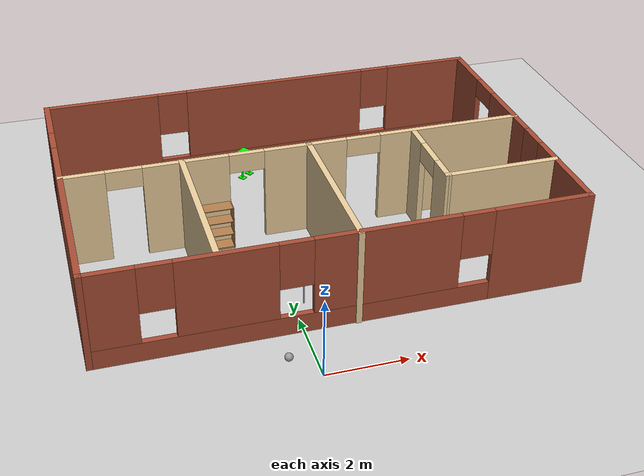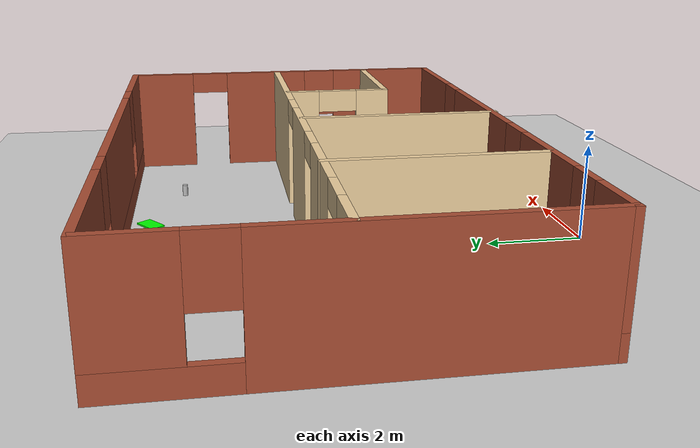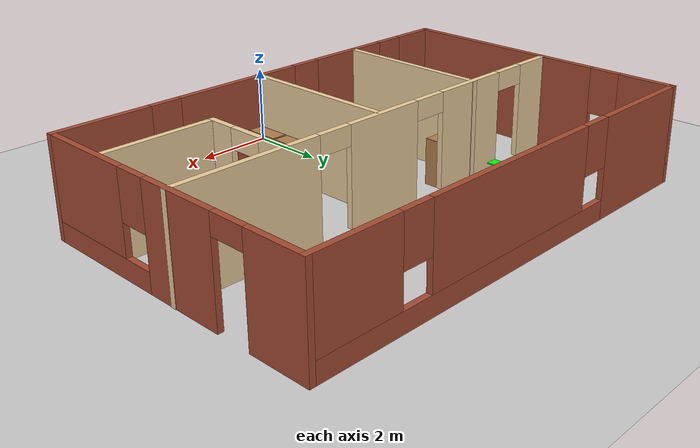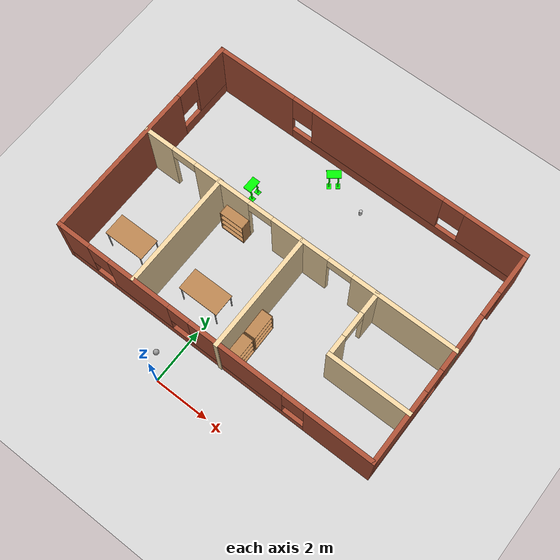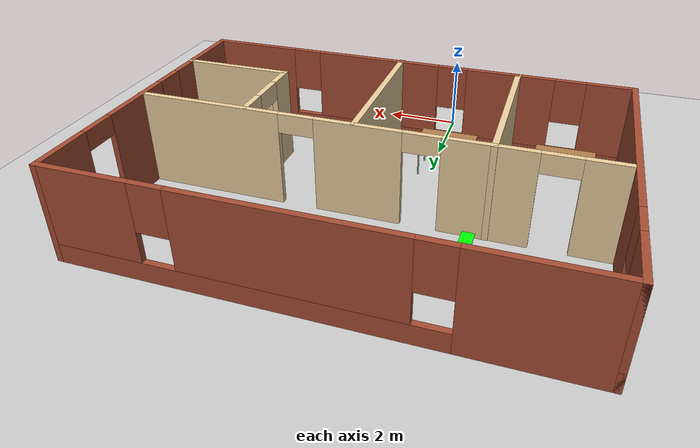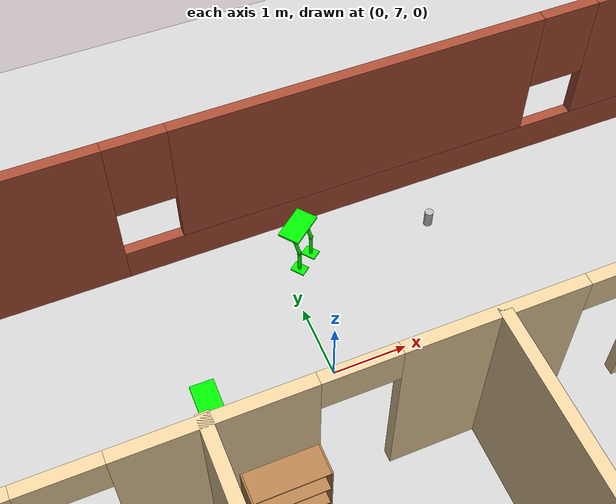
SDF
<sdf version="1.7">
 <world name="default">
  <plugin name="welcome_message" filename="libwelcome_message.so"/>
  <light name="sun" type="directional">
   <pose>0 0 10 0 -0 0</pose>
   <diffuse>0.8 0.8 0.8 1</diffuse>
   <specular>0.2 0.2 0.2 1</specular>
   <attenuation>
    <range>1000</range>
    <constant>0.9</constant>
    <linear>0.01</linear>
    <quadratic>0.001</quadratic>
   </attenuation>
   <direction>-0.5 0.1 -0.9</direction>
   <spot><inner_angle>0</inner_angle><outer_angle>0</outer_angle><falloff>0</falloff></spot>
  </light>
  <model name="ground_plane">
   <static>1</static>
   <link name="link">
    <collision name="collision">
     <geometry><plane><normal>0 0 1</normal><size>100 100</size></plane></geometry>
     <surface>
      <contact><collide_bitmask>65535</collide_bitmask></contact>
      <friction><ode><mu>100</mu><mu2>50</mu2></ode></friction>
     </surface>
    </collision>
    <visual name="visual">
     <cast_shadows>0</cast_shadows>
     <geometry><plane><normal>0 0 1</normal><size>100 100</size></plane></geometry>
     <material>
      <script><uri>file://media/materials/scripts/gazebo.material</uri><name>Gazebo/Grey</name></script>
     </material>
    </visual>
   </link>
  </model>
  <gravity>0 0 -9.8</gravity>
  <magnetic_field>6e-06 2.3e-05 -4.2e-05</magnetic_field>
  <atmosphere type="adiabatic"/>
  <physics name="default_physics" default="0" type="ode">
   <max_step_size>0.001</max_step_size>
   <real_time_factor>1</real_time_factor>
   <real_time_update_rate>1000</real_time_update_rate>
  </physics>
  <scene><ambient>0.4 0.4 0.4 1</ambient><background>0.7 0.7 0.7 1</background><shadows>1</shadows></scene>
  <spherical_coordinates>
   <surface_model>EARTH_WGS84</surface_model>
   <latitude_deg>0</latitude_deg>
   <longitude_deg>0</longitude_deg>
   <elevation>0</elevation>
   <heading_deg>0</heading_deg>
  </spherical_coordinates>
  <model name="Building">
   <pose>1.04028 5.52884 0 0 -0 0</pose>
   <link name="Wall_0">
    <pose>-5.93028 0.01616 0 0 -0 1.5708</pose>
    <visual name="Wall_0_Visual_0">
     <pose>-1.14394 0 1.25 0 -0 0</pose>
     <geometry><box><size>5.71213 0.15 2.5</size></box></geometry>
     <material>
      <script><uri>file://media/materials/scripts/gazebo.material</uri><name>Gazebo/Bricks</name></script>
      <ambient>1 1 1 1</ambient>
     </material>
     <meta><layer>0</layer></meta>
    </visual>
    <collision name="Wall_0_Collision_0">
     <geometry><box><size>5.71213 0.15 2.5</size></box></geometry>
     <pose>-1.14394 0 1.25 0 -0 0</pose>
    </collision>
    <visual name="Wall_0_Visual_1">
     <pose>2.85606 0 0.25 0 -0 0</pose>
     <geometry><box><size>2.28788 0.15 0.5</size></box></geometry>
     <material>
      <script><uri>file://media/materials/scripts/gazebo.material</uri><name>Gazebo/Bricks</name></script>
      <ambient>1 1 1 1</ambient>
     </material>
     <meta><layer>0</layer></meta>
    </visual>
    <collision name="Wall_0_Collision_1">
     <geometry><box><size>2.28788 0.15 0.5</size></box></geometry>
     <pose>2.85606 0 0.25 0 -0 0</pose>
    </collision>
    <visual name="Wall_0_Visual_2">
     <pose>3.25606 0 1.5 0 -0 0</pose>
     <geometry><box><size>1.48788 0.15 2</size></box></geometry>
     <material>
      <script><uri>file://media/materials/scripts/gazebo.material</uri><name>Gazebo/Bricks</name></script>
      <ambient>1 1 1 1</ambient>
     </material>
     <meta><layer>0</layer></meta>
    </visual>
    <collision name="Wall_0_Collision_2">
     <geometry><box><size>1.48788 0.15 2</size></box></geometry>
     <pose>3.25606 0 1.5 0 -0 0</pose>
    </collision>
    <visual name="Wall_0_Visual_3">
     <pose>2.11212 0 1.9 0 -0 0</pose>
     <geometry><box><size>0.8 0.15 1.2</size></box></geometry>
     <material>
      <script><uri>file://media/materials/scripts/gazebo.material</uri><name>Gazebo/Bricks</name></script>
      <ambient>1 1 1 1</ambient>
     </material>
     <meta><layer>0</layer></meta>
    </visual>
    <collision name="Wall_0_Collision_3">
     <geometry><box><size>0.8 0.15 1.2</size></box></geometry>
     <pose>2.11212 0 1.9 0 -0 0</pose>
    </collision>
   </link>
   <link name="Wall_1">
    <pose>-0.005278 3.94116 0 0 -0 0</pose>
    <visual name="Wall_1_Visual_0">
     <pose>-4.47581 0 1.25 0 -0 0</pose>
     <geometry><box><size>3.04838 0.15 2.5</size></box></geometry>
     <material>
      <script><uri>file://media/materials/scripts/gazebo.material</uri><name>Gazebo/Bricks</name></script>
      <ambient>1 1 1 1</ambient>
     </material>
     <meta><layer>0</layer></meta>
    </visual>
    <collision name="Wall_1_Collision_0">
     <geometry><box><size>3.04838 0.15 2.5</size></box></geometry>
     <pose>-4.47581 0 1.25 0 -0 0</pose>
    </collision>
    <visual name="Wall_1_Visual_1">
     <pose>1.52419 0 0.25 0 -0 0</pose>
     <geometry><box><size>8.95162 0.15 0.5</size></box></geometry>
     <material>
      <script><uri>file://media/materials/scripts/gazebo.material</uri><name>Gazebo/Bricks</name></script>
      <ambient>1 1 1 1</ambient>
     </material>
     <meta><layer>0</layer></meta>
    </visual>
    <collision name="Wall_1_Collision_1">
     <geometry><box><size>8.95162 0.15 0.5</size></box></geometry>
     <pose>1.52419 0 0.25 0 -0 0</pose>
    </collision>
    <visual name="Wall_1_Visual_2">
     <pose>0.370959 0 1.5 0 -0 0</pose>
     <geometry><box><size>5.04515 0.15 2</size></box></geometry>
     <material>
      <script><uri>file://media/materials/scripts/gazebo.material</uri><name>Gazebo/Bricks</name></script>
      <ambient>1 1 1 1</ambient>
     </material>
     <meta><layer>0</layer></meta>
    </visual>
    <collision name="Wall_1_Collision_2">
     <geometry><box><size>5.04515 0.15 2</size></box></geometry>
     <pose>0.370959 0 1.5 0 -0 0</pose>
    </collision>
    <visual name="Wall_1_Visual_3">
     <pose>4.84677 0 1.5 0 -0 0</pose>
     <geometry><box><size>2.30647 0.15 2</size></box></geometry>
     <material>
      <script><uri>file://media/materials/scripts/gazebo.material</uri><name>Gazebo/Bricks</name></script>
      <ambient>1 1 1 1</ambient>
     </material>
     <meta><layer>0</layer></meta>
    </visual>
    <collision name="Wall_1_Collision_3">
     <geometry><box><size>2.30647 0.15 2</size></box></geometry>
     <pose>4.84677 0 1.5 0 -0 0</pose>
    </collision>
    <visual name="Wall_1_Visual_4">
     <pose>-2.55162 0 1.9 0 -0 0</pose>
     <geometry><box><size>0.8 0.15 1.2</size></box></geometry>
     <material>
      <script><uri>file://media/materials/scripts/gazebo.material</uri><name>Gazebo/Bricks</name></script>
      <ambient>1 1 1 1</ambient>
     </material>
     <meta><layer>0</layer></meta>
    </visual>
    <collision name="Wall_1_Collision_4">
     <geometry><box><size>0.8 0.15 1.2</size></box></geometry>
     <pose>-2.55162 0 1.9 0 -0 0</pose>
    </collision>
    <visual name="Wall_1_Visual_5">
     <pose>3.29353 0 1.9 0 -0 0</pose>
     <geometry><box><size>0.8 0.15 1.2</size></box></geometry>
     <material>
      <script><uri>file://media/materials/scripts/gazebo.material</uri><name>Gazebo/Bricks</name></script>
      <ambient>1 1 1 1</ambient>
     </material>
     <meta><layer>0</layer></meta>
    </visual>
    <collision name="Wall_1_Collision_5">
     <geometry><box><size>0.8 0.15 1.2</size></box></geometry>
     <pose>3.29353 0 1.9 0 -0 0</pose>
    </collision>
   </link>
   <link name="Wall_11">
    <collision name="Wall_11_Collision">
     <geometry><box><size>4.25 0.15 2.5</size></box></geometry>
     <pose>0 0 1.25 0 -0 0</pose>
    </collision>
    <visual name="Wall_11_Visual">
     <pose>0 0 1.25 0 -0 0</pose>
     <geometry><box><size>4.25 0.15 2.5</size></box></geometry>
     <material>
      <script><uri>file://media/materials/scripts/gazebo.material</uri><name>Gazebo/Grey</name></script>
      <ambient>0.921569 0.807843 0.615686 1</ambient>
     </material>
     <meta><layer>0</layer></meta>
    </visual>
    <pose>0.272165 -1.89116 0 0 0 -1.5708</pose>
   </link>
   <link name="Wall_13">
    <pose>3.06519 -0.98956 0 0 0 -1.5708</pose>
    <visual name="Wall_13_Visual_0">
     <pose>-0.838996 0 1.25 0 -0 0</pose>
     <geometry><box><size>0.822009 0.15 2.5</size></box></geometry>
     <material>
      <script><uri>file://media/materials/scripts/gazebo.material</uri><name>Gazebo/Grey</name></script>
      <ambient>0.921569 0.807843 0.615686 1</ambient>
     </material>
     <meta><layer>0</layer></meta>
    </visual>
    <collision name="Wall_13_Collision_0">
     <geometry><box><size>0.822009 0.15 2.5</size></box></geometry>
     <pose>-0.838996 0 1.25 0 -0 0</pose>
    </collision>
    <visual name="Wall_13_Visual_1">
     <pose>0.861004 0 1.25 0 -0 0</pose>
     <geometry><box><size>0.777991 0.15 2.5</size></box></geometry>
     <material>
      <script><uri>file://media/materials/scripts/gazebo.material</uri><name>Gazebo/Grey</name></script>
      <ambient>0.921569 0.807843 0.615686 1</ambient>
     </material>
     <meta><layer>0</layer></meta>
    </visual>
    <collision name="Wall_13_Collision_1">
     <geometry><box><size>0.777991 0.15 2.5</size></box></geometry>
     <pose>0.861004 0 1.25 0 -0 0</pose>
    </collision>
    <visual name="Wall_13_Visual_2">
     <pose>0.022009 0 2.25 0 -0 0</pose>
     <geometry><box><size>0.9 0.15 0.5</size></box></geometry>
     <material>
      <script><uri>file://media/materials/scripts/gazebo.material</uri><name>Gazebo/Grey</name></script>
      <ambient>0.921569 0.807843 0.615686 1</ambient>
     </material>
     <meta><layer>0</layer></meta>
    </visual>
    <collision name="Wall_13_Collision_2">
     <geometry><box><size>0.9 0.15 0.5</size></box></geometry>
     <pose>0.022009 0 2.25 0 -0 0</pose>
    </collision>
   </link>
   <link name="Wall_14">
    <collision name="Wall_14_Collision">
     <geometry><box><size>3 0.15 2.5</size></box></geometry>
     <pose>0 0 1.25 0 -0 0</pose>
    </collision>
    <visual name="Wall_14_Visual">
     <pose>0 0 1.25 0 -0 0</pose>
     <geometry><box><size>3 0.15 2.5</size></box></geometry>
     <material>
      <script><uri>file://media/materials/scripts/gazebo.material</uri><name>Gazebo/Grey</name></script>
      <ambient>0.921569 0.807843 0.615686 1</ambient>
     </material>
     <meta><layer>0</layer></meta>
    </visual>
    <pose>4.49019 -2.16456 0 0 -0 0</pose>
   </link>
   <link name="Wall_2">
    <pose>5.91972 0.01616 0 0 0 -1.5708</pose>
    <visual name="Wall_2_Visual_0">
     <pose>-3.21405 0 1.25 0 -0 0</pose>
     <geometry><box><size>1.57191 0.15 2.5</size></box></geometry>
     <material>
      <script><uri>file://media/materials/scripts/gazebo.material</uri><name>Gazebo/Bricks</name></script>
      <ambient>1 1 1 1</ambient>
     </material>
     <meta><layer>0</layer></meta>
    </visual>
    <collision name="Wall_2_Collision_0">
     <geometry><box><size>1.57191 0.15 2.5</size></box></geometry>
     <pose>-3.21405 0 1.25 0 -0 0</pose>
    </collision>
    <visual name="Wall_2_Visual_1">
     <pose>-0.481912 0 1.25 0 -0 0</pose>
     <geometry><box><size>2.09236 0.15 2.5</size></box></geometry>
     <material>
      <script><uri>file://media/materials/scripts/gazebo.material</uri><name>Gazebo/Bricks</name></script>
      <ambient>1 1 1 1</ambient>
     </material>
     <meta><layer>0</layer></meta>
    </visual>
    <collision name="Wall_2_Collision_1">
     <geometry><box><size>2.09236 0.15 2.5</size></box></geometry>
     <pose>-0.481912 0 1.25 0 -0 0</pose>
    </collision>
    <visual name="Wall_2_Visual_2">
     <pose>2.28213 0 0.25 0 -0 0</pose>
     <geometry><box><size>3.43573 0.15 0.5</size></box></geometry>
     <material>
      <script><uri>file://media/materials/scripts/gazebo.material</uri><name>Gazebo/Bricks</name></script>
      <ambient>1 1 1 1</ambient>
     </material>
     <meta><layer>0</layer></meta>
    </visual>
    <collision name="Wall_2_Collision_2">
     <geometry><box><size>3.43573 0.15 0.5</size></box></geometry>
     <pose>2.28213 0 0.25 0 -0 0</pose>
    </collision>
    <visual name="Wall_2_Visual_3">
     <pose>2.68214 0 1.5 0 -0 0</pose>
     <geometry><box><size>2.63573 0.15 2</size></box></geometry>
     <material>
      <script><uri>file://media/materials/scripts/gazebo.material</uri><name>Gazebo/Bricks</name></script>
      <ambient>1 1 1 1</ambient>
     </material>
     <meta><layer>0</layer></meta>
    </visual>
    <collision name="Wall_2_Collision_3">
     <geometry><box><size>2.63573 0.15 2</size></box></geometry>
     <pose>2.68214 0 1.5 0 -0 0</pose>
    </collision>
    <visual name="Wall_2_Visual_4">
     <pose>0.964269 0 1.9 0 -0 0</pose>
     <geometry><box><size>0.8 0.15 1.2</size></box></geometry>
     <material>
      <script><uri>file://media/materials/scripts/gazebo.material</uri><name>Gazebo/Bricks</name></script>
      <ambient>1 1 1 1</ambient>
     </material>
     <meta><layer>0</layer></meta>
    </visual>
    <collision name="Wall_2_Collision_4">
     <geometry><box><size>0.8 0.15 1.2</size></box></geometry>
     <pose>0.964269 0 1.9 0 -0 0</pose>
    </collision>
    <visual name="Wall_2_Visual_5">
     <pose>-1.97809 0 2.25 0 -0 0</pose>
     <geometry><box><size>0.9 0.15 0.5</size></box></geometry>
     <material>
      <script><uri>file://media/materials/scripts/gazebo.material</uri><name>Gazebo/Bricks</name></script>
      <ambient>1 1 1 1</ambient>
     </material>
     <meta><layer>0</layer></meta>
    </visual>
    <collision name="Wall_2_Collision_5">
     <geometry><box><size>0.9 0.15 0.5</size></box></geometry>
     <pose>-1.97809 0 2.25 0 -0 0</pose>
    </collision>
   </link>
   <link name="Wall_3">
    <pose>-0.005278 -3.90884 0 0 -0 3.14159</pose>
    <visual name="Wall_3_Visual_0">
     <pose>-4.75448 0 1.25 0 -0 0</pose>
     <geometry><box><size>2.49105 0.15 2.5</size></box></geometry>
     <material>
      <script><uri>file://media/materials/scripts/gazebo.material</uri><name>Gazebo/Bricks</name></script>
      <ambient>1 1 1 1</ambient>
     </material>
     <meta><layer>0</layer></meta>
    </visual>
    <collision name="Wall_3_Collision_0">
     <geometry><box><size>2.49105 0.15 2.5</size></box></geometry>
     <pose>-4.75448 0 1.25 0 -0 0</pose>
    </collision>
    <visual name="Wall_3_Visual_1">
     <pose>1.24552 0 0.25 0 -0 0</pose>
     <geometry><box><size>9.50895 0.15 0.5</size></box></geometry>
     <material>
      <script><uri>file://media/materials/scripts/gazebo.material</uri><name>Gazebo/Bricks</name></script>
      <ambient>1 1 1 1</ambient>
     </material>
     <meta><layer>0</layer></meta>
    </visual>
    <collision name="Wall_3_Collision_1">
     <geometry><box><size>9.50895 0.15 0.5</size></box></geometry>
     <pose>1.24552 0 0.25 0 -0 0</pose>
    </collision>
    <visual name="Wall_3_Visual_2">
     <pose>-0.955473 0 1.5 0 -0 0</pose>
     <geometry><box><size>3.50695 0.15 2</size></box></geometry>
     <material>
      <script><uri>file://media/materials/scripts/gazebo.material</uri><name>Gazebo/Bricks</name></script>
      <ambient>1 1 1 1</ambient>
     </material>
     <meta><layer>0</layer></meta>
    </visual>
    <collision name="Wall_3_Collision_2">
     <geometry><box><size>3.50695 0.15 2</size></box></geometry>
     <pose>-0.955473 0 1.5 0 -0 0</pose>
    </collision>
    <visual name="Wall_3_Visual_3">
     <pose>2.76696 0 1.5 0 -0 0</pose>
     <geometry><box><size>2.33792 0.15 2</size></box></geometry>
     <material>
      <script><uri>file://media/materials/scripts/gazebo.material</uri><name>Gazebo/Bricks</name></script>
      <ambient>1 1 1 1</ambient>
     </material>
     <meta><layer>0</layer></meta>
    </visual>
    <collision name="Wall_3_Collision_3">
     <geometry><box><size>2.33792 0.15 2</size></box></geometry>
     <pose>2.76696 0 1.5 0 -0 0</pose>
    </collision>
    <visual name="Wall_3_Visual_4">
     <pose>5.36796 0 1.5 0 -0 0</pose>
     <geometry><box><size>1.26408 0.15 2</size></box></geometry>
     <material>
      <script><uri>file://media/materials/scripts/gazebo.material</uri><name>Gazebo/Bricks</name></script>
      <ambient>1 1 1 1</ambient>
     </material>
     <meta><layer>0</layer></meta>
    </visual>
    <collision name="Wall_3_Collision_4">
     <geometry><box><size>1.26408 0.15 2</size></box></geometry>
     <pose>5.36796 0 1.5 0 -0 0</pose>
    </collision>
    <visual name="Wall_3_Visual_5">
     <pose>-3.10895 0 1.9 0 -0 0</pose>
     <geometry><box><size>0.8 0.15 1.2</size></box></geometry>
     <material>
      <script><uri>file://media/materials/scripts/gazebo.material</uri><name>Gazebo/Bricks</name></script>
      <ambient>1 1 1 1</ambient>
     </material>
     <meta><layer>0</layer></meta>
    </visual>
    <collision name="Wall_3_Collision_5">
     <geometry><box><size>0.8 0.15 1.2</size></box></geometry>
     <pose>-3.10895 0 1.9 0 -0 0</pose>
    </collision>
    <visual name="Wall_3_Visual_6">
     <pose>1.198 0 1.9 0 -0 0</pose>
     <geometry><box><size>0.8 0.15 1.2</size></box></geometry>
     <material>
      <script><uri>file://media/materials/scripts/gazebo.material</uri><name>Gazebo/Bricks</name></script>
      <ambient>1 1 1 1</ambient>
     </material>
     <meta><layer>0</layer></meta>
    </visual>
    <collision name="Wall_3_Collision_6">
     <geometry><box><size>0.8 0.15 1.2</size></box></geometry>
     <pose>1.198 0 1.9 0 -0 0</pose>
    </collision>
    <visual name="Wall_3_Visual_7">
     <pose>4.33592 0 1.9 0 -0 0</pose>
     <geometry><box><size>0.8 0.15 1.2</size></box></geometry>
     <material>
      <script><uri>file://media/materials/scripts/gazebo.material</uri><name>Gazebo/Bricks</name></script>
      <ambient>1 1 1 1</ambient>
     </material>
     <meta><layer>0</layer></meta>
    </visual>
    <collision name="Wall_3_Collision_7">
     <geometry><box><size>0.8 0.15 1.2</size></box></geometry>
     <pose>4.33592 0 1.9 0 -0 0</pose>
    </collision>
   </link>
   <link name="Wall_5">
    <pose>0.005278 0.194603 0 0 -0 0</pose>
    <visual name="Wall_5_Visual_0">
     <pose>-5.43237 0 1.25 0 -0 0</pose>
     <geometry><box><size>1.13525 0.15 2.5</size></box></geometry>
     <material>
      <script><uri>file://media/materials/scripts/gazebo.material</uri><name>Gazebo/Grey</name></script>
      <ambient>0.921569 0.807843 0.615686 1</ambient>
     </material>
     <meta><layer>0</layer></meta>
    </visual>
    <collision name="Wall_5_Collision_0">
     <geometry><box><size>1.13525 0.15 2.5</size></box></geometry>
     <pose>-5.43237 0 1.25 0 -0 0</pose>
    </collision>
    <visual name="Wall_5_Visual_1">
     <pose>-2.88524 0 1.25 0 -0 0</pose>
     <geometry><box><size>2.15902 0.15 2.5</size></box></geometry>
     <material>
      <script><uri>file://media/materials/scripts/gazebo.material</uri><name>Gazebo/Grey</name></script>
      <ambient>0.921569 0.807843 0.615686 1</ambient>
     </material>
     <meta><layer>0</layer></meta>
    </visual>
    <collision name="Wall_5_Collision_1">
     <geometry><box><size>2.15902 0.15 2.5</size></box></geometry>
     <pose>-2.88524 0 1.25 0 -0 0</pose>
    </collision>
    <visual name="Wall_5_Visual_2">
     <pose>0.173787 0 1.25 0 -0 0</pose>
     <geometry><box><size>2.15902 0.15 2.5</size></box></geometry>
     <material>
      <script><uri>file://media/materials/scripts/gazebo.material</uri><name>Gazebo/Grey</name></script>
      <ambient>0.921569 0.807843 0.615686 1</ambient>
     </material>
     <meta><layer>0</layer></meta>
    </visual>
    <collision name="Wall_5_Collision_2">
     <geometry><box><size>2.15902 0.15 2.5</size></box></geometry>
     <pose>0.173787 0 1.25 0 -0 0</pose>
    </collision>
    <visual name="Wall_5_Visual_3">
     <pose>4.07665 0 1.25 0 -0 0</pose>
     <geometry><box><size>3.8467 0.15 2.5</size></box></geometry>
     <material>
      <script><uri>file://media/materials/scripts/gazebo.material</uri><name>Gazebo/Grey</name></script>
      <ambient>0.921569 0.807843 0.615686 1</ambient>
     </material>
     <meta><layer>0</layer></meta>
    </visual>
    <collision name="Wall_5_Collision_3">
     <geometry><box><size>3.8467 0.15 2.5</size></box></geometry>
     <pose>4.07665 0 1.25 0 -0 0</pose>
    </collision>
    <visual name="Wall_5_Visual_4">
     <pose>-4.41475 0 2.25 0 -0 0</pose>
     <geometry><box><size>0.9 0.15 0.5</size></box></geometry>
     <material>
      <script><uri>file://media/materials/scripts/gazebo.material</uri><name>Gazebo/Grey</name></script>
      <ambient>0.921569 0.807843 0.615686 1</ambient>
     </material>
     <meta><layer>0</layer></meta>
    </visual>
    <collision name="Wall_5_Collision_4">
     <geometry><box><size>0.9 0.15 0.5</size></box></geometry>
     <pose>-4.41475 0 2.25 0 -0 0</pose>
    </collision>
    <visual name="Wall_5_Visual_5">
     <pose>-1.35573 0 2.25 0 -0 0</pose>
     <geometry><box><size>0.9 0.15 0.5</size></box></geometry>
     <material>
      <script><uri>file://media/materials/scripts/gazebo.material</uri><name>Gazebo/Grey</name></script>
      <ambient>0.921569 0.807843 0.615686 1</ambient>
     </material>
     <meta><layer>0</layer></meta>
    </visual>
    <collision name="Wall_5_Collision_5">
     <geometry><box><size>0.9 0.15 0.5</size></box></geometry>
     <pose>-1.35573 0 2.25 0 -0 0</pose>
    </collision>
    <visual name="Wall_5_Visual_6">
     <pose>1.7033 0 2.25 0 -0 0</pose>
     <geometry><box><size>0.9 0.15 0.5</size></box></geometry>
     <material>
      <script><uri>file://media/materials/scripts/gazebo.material</uri><name>Gazebo/Grey</name></script>
      <ambient>0.921569 0.807843 0.615686 1</ambient>
     </material>
     <meta><layer>0</layer></meta>
    </visual>
    <collision name="Wall_5_Collision_6">
     <geometry><box><size>0.9 0.15 0.5</size></box></geometry>
     <pose>1.7033 0 2.25 0 -0 0</pose>
    </collision>
   </link>
   <link name="Wall_9">
    <collision name="Wall_9_Collision">
     <geometry><box><size>4.25 0.15 2.5</size></box></geometry>
     <pose>0 0 1.25 0 -0 0</pose>
    </collision>
    <visual name="Wall_9_Visual">
     <pose>0 0 1.25 0 -0 0</pose>
     <geometry><box><size>4.25 0.15 2.5</size></box></geometry>
     <material>
      <script><uri>file://media/materials/scripts/gazebo.material</uri><name>Gazebo/Grey</name></script>
      <ambient>0.921569 0.807843 0.615686 1</ambient>
     </material>
     <meta><layer>0</layer></meta>
    </visual>
    <pose>-2.97306 -1.83796 0 0 0 -1.5708</pose>
   </link>
   <static>1</static>
  </model>
  <model name="table">
   <static>1</static>
   <link name="link">
    <collision name="surface">
     <pose>0 0 1 0 -0 0</pose>
     <geometry><box><size>1.5 0.8 0.03</size></box></geometry>
     <surface><friction><ode><mu>0.6</mu><mu2>0.6</mu2></ode></friction></surface>
    </collision>
    <visual name="visual1">
     <pose>0 0 1 0 -0 0</pose>
     <geometry><box><size>1.5 0.8 0.03</size></box></geometry>
     <material>
      <script><uri>file://media/materials/scripts/gazebo.material</uri><name>Gazebo/Wood</name></script>
     </material>
    </visual>
    <collision name="front_left_leg">
     <pose>0.68 0.38 0.5 0 -0 0</pose>
     <geometry><cylinder><radius>0.02</radius><length>1</length></cylinder></geometry>
    </collision>
    <visual name="front_left_leg">
     <pose>0.68 0.38 0.5 0 -0 0</pose>
     <geometry><cylinder><radius>0.02</radius><length>1</length></cylinder></geometry>
     <material>
      <script><uri>file://media/materials/scripts/gazebo.material</uri><name>Gazebo/Grey</name></script>
     </material>
    </visual>
    <collision name="front_right_leg">
     <pose>0.68 -0.38 0.5 0 -0 0</pose>
     <geometry><cylinder><radius>0.02</radius><length>1</length></cylinder></geometry>
    </collision>
    <visual name="front_right_leg">
     <pose>0.68 -0.38 0.5 0 -0 0</pose>
     <geometry><cylinder><radius>0.02</radius><length>1</length></cylinder></geometry>
     <material>
      <script><uri>file://media/materials/scripts/gazebo.material</uri><name>Gazebo/Grey</name></script>
     </material>
    </visual>
    <collision name="back_right_leg">
     <pose>-0.68 -0.38 0.5 0 -0 0</pose>
     <geometry><cylinder><radius>0.02</radius><length>1</length></cylinder></geometry>
    </collision>
    <visual name="back_right_leg">
     <pose>-0.68 -0.38 0.5 0 -0 0</pose>
     <geometry><cylinder><radius>0.02</radius><length>1</length></cylinder></geometry>
     <material>
      <script><uri>file://media/materials/scripts/gazebo.material</uri><name>Gazebo/Grey</name></script>
     </material>
    </visual>
    <collision name="back_left_leg">
     <pose>-0.68 0.38 0.5 0 -0 0</pose>
     <geometry><cylinder><radius>0.02</radius><length>1</length></cylinder></geometry>
    </collision>
    <visual name="back_left_leg">
     <pose>-0.68 0.38 0.5 0 -0 0</pose>
     <geometry><cylinder><radius>0.02</radius><length>1</length></cylinder></geometry>
     <material>
      <script><uri>file://media/materials/scripts/gazebo.material</uri><name>Gazebo/Grey</name></script>
     </material>
    </visual>
   </link>
   <pose>-0.388248 2.97596 0 0 -0 0</pose>
  </model>
  <model name="table_0">
   <static>1</static>
   <link name="link">
    <collision name="surface">
     <pose>0 0 1 0 -0 0</pose>
     <geometry><box><size>1.5 0.8 0.03</size></box></geometry>
     <surface><friction><ode><mu>0.6</mu><mu2>0.6</mu2></ode></friction></surface>
    </collision>
    <visual name="visual1">
     <pose>0 0 1 0 -0 0</pose>
     <geometry><box><size>1.5 0.8 0.03</size></box></geometry>
     <material>
      <script><uri>file://media/materials/scripts/gazebo.material</uri><name>Gazebo/Wood</name></script>
     </material>
    </visual>
    <collision name="front_left_leg">
     <pose>0.68 0.38 0.5 0 -0 0</pose>
     <geometry><cylinder><radius>0.02</radius><length>1</length></cylinder></geometry>
    </collision>
    <visual name="front_left_leg">
     <pose>0.68 0.38 0.5 0 -0 0</pose>
     <geometry><cylinder><radius>0.02</radius><length>1</length></cylinder></geometry>
     <material>
      <script><uri>file://media/materials/scripts/gazebo.material</uri><name>Gazebo/Grey</name></script>
     </material>
    </visual>
    <collision name="front_right_leg">
     <pose>0.68 -0.38 0.5 0 -0 0</pose>
     <geometry><cylinder><radius>0.02</radius><length>1</length></cylinder></geometry>
    </collision>
    <visual name="front_right_leg">
     <pose>0.68 -0.38 0.5 0 -0 0</pose>
     <geometry><cylinder><radius>0.02</radius><length>1</length></cylinder></geometry>
     <material>
      <script><uri>file://media/materials/scripts/gazebo.material</uri><name>Gazebo/Grey</name></script>
     </material>
    </visual>
    <collision name="back_right_leg">
     <pose>-0.68 -0.38 0.5 0 -0 0</pose>
     <geometry><cylinder><radius>0.02</radius><length>1</length></cylinder></geometry>
    </collision>
    <visual name="back_right_leg">
     <pose>-0.68 -0.38 0.5 0 -0 0</pose>
     <geometry><cylinder><radius>0.02</radius><length>1</length></cylinder></geometry>
     <material>
      <script><uri>file://media/materials/scripts/gazebo.material</uri><name>Gazebo/Grey</name></script>
     </material>
    </visual>
    <collision name="back_left_leg">
     <pose>-0.68 0.38 0.5 0 -0 0</pose>
     <geometry><cylinder><radius>0.02</radius><length>1</length></cylinder></geometry>
    </collision>
    <visual name="back_left_leg">
     <pose>-0.68 0.38 0.5 0 -0 0</pose>
     <geometry><cylinder><radius>0.02</radius><length>1</length></cylinder></geometry>
     <material>
      <script><uri>file://media/materials/scripts/gazebo.material</uri><name>Gazebo/Grey</name></script>
     </material>
    </visual>
   </link>
   <pose>-3.44406 2.96738 0 0 -0 0</pose>
  </model>
  <model name="bookshelf">
   <static>1</static>
   <link name="link">
    <inertial><mass>1</mass></inertial>
    <collision name="back">
     <pose>0 0.005 0.6 0 -0 0</pose>
     <geometry><box><size>0.9 0.01 1.2</size></box></geometry>
    </collision>
    <visual name="visual1">
     <pose>0 0.005 0.6 0 -0 0</pose>
     <geometry><box><size>0.9 0.01 1.2</size></box></geometry>
     <material>
      <script><uri>file://media/materials/scripts/gazebo.material</uri><name>Gazebo/Wood</name></script>
     </material>
    </visual>
    <collision name="left_side">
     <pose>0.45 -0.195 0.6 0 -0 0</pose>
     <geometry><box><size>0.02 0.4 1.2</size></box></geometry>
    </collision>
    <visual name="visual2">
     <pose>0.45 -0.195 0.6 0 -0 0</pose>
     <geometry><box><size>0.02 0.4 1.2</size></box></geometry>
     <material>
      <script><uri>file://media/materials/scripts/gazebo.material</uri><name>Gazebo/Wood</name></script>
     </material>
    </visual>
    <collision name="right_side">
     <pose>-0.45 -0.195 0.6 0 -0 0</pose>
     <geometry><box><size>0.02 0.4 1.2</size></box></geometry>
    </collision>
    <visual name="visual3">
     <pose>-0.45 -0.195 0.6 0 -0 0</pose>
     <geometry><box><size>0.02 0.4 1.2</size></box></geometry>
     <material>
      <script><uri>file://media/materials/scripts/gazebo.material</uri><name>Gazebo/Wood</name></script>
     </material>
    </visual>
    <collision name="bottom">
     <pose>0 -0.195 0.03 0 -0 0</pose>
     <geometry><box><size>0.88 0.4 0.06</size></box></geometry>
    </collision>
    <visual name="visual4">
     <pose>0 -0.195 0.03 0 -0 0</pose>
     <geometry><box><size>0.88 0.4 0.06</size></box></geometry>
     <material>
      <script><uri>file://media/materials/scripts/gazebo.material</uri><name>Gazebo/Wood</name></script>
     </material>
    </visual>
    <collision name="top">
     <pose>0 -0.195 1.19 0 -0 0</pose>
     <geometry><box><size>0.88 0.4 0.02</size></box></geometry>
    </collision>
    <visual name="visual5">
     <pose>0 -0.195 1.19 0 -0 0</pose>
     <geometry><box><size>0.88 0.4 0.02</size></box></geometry>
     <material>
      <script><uri>file://media/materials/scripts/gazebo.material</uri><name>Gazebo/Wood</name></script>
     </material>
    </visual>
    <collision name="low_shelf">
     <pose>0 -0.195 0.43 0 -0 0</pose>
     <geometry><box><size>0.88 0.4 0.02</size></box></geometry>
    </collision>
    <visual name="visual6">
     <pose>0 -0.195 0.43 0 -0 0</pose>
     <geometry><box><size>0.88 0.4 0.02</size></box></geometry>
     <material>
      <script><uri>file://media/materials/scripts/gazebo.material</uri><name>Gazebo/Wood</name></script>
     </material>
    </visual>
    <collision name="high_shelf">
     <pose>0 -0.195 0.8 0 -0 0</pose>
     <geometry><box><size>0.88 0.4 0.02</size></box></geometry>
    </collision>
    <visual name="visual7">
     <pose>0 -0.195 0.8 0 -0 0</pose>
     <geometry><box><size>0.88 0.4 0.02</size></box></geometry>
     <material>
      <script><uri>file://media/materials/scripts/gazebo.material</uri><name>Gazebo/Wood</name></script>
     </material>
    </visual>
   </link>
   <pose>-1.22377 5.6787 0 0 -0 0</pose>
  </model>
  <model name="bookshelf_0">
   <static>1</static>
   <link name="link">
    <inertial><mass>1</mass></inertial>
    <collision name="back">
     <pose>0 0.005 0.6 0 -0 0</pose>
     <geometry><box><size>0.9 0.01 1.2</size></box></geometry>
    </collision>
    <visual name="visual1">
     <pose>0 0.005 0.6 0 -0 0</pose>
     <geometry><box><size>0.9 0.01 1.2</size></box></geometry>
     <material>
      <script><uri>file://media/materials/scripts/gazebo.material</uri><name>Gazebo/Wood</name></script>
     </material>
    </visual>
    <collision name="left_side">
     <pose>0.45 -0.195 0.6 0 -0 0</pose>
     <geometry><box><size>0.02 0.4 1.2</size></box></geometry>
    </collision>
    <visual name="visual2">
     <pose>0.45 -0.195 0.6 0 -0 0</pose>
     <geometry><box><size>0.02 0.4 1.2</size></box></geometry>
     <material>
      <script><uri>file://media/materials/scripts/gazebo.material</uri><name>Gazebo/Wood</name></script>
     </material>
    </visual>
    <collision name="right_side">
     <pose>-0.45 -0.195 0.6 0 -0 0</pose>
     <geometry><box><size>0.02 0.4 1.2</size></box></geometry>
    </collision>
    <visual name="visual3">
     <pose>-0.45 -0.195 0.6 0 -0 0</pose>
     <geometry><box><size>0.02 0.4 1.2</size></box></geometry>
     <material>
      <script><uri>file://media/materials/scripts/gazebo.material</uri><name>Gazebo/Wood</name></script>
     </material>
    </visual>
    <collision name="bottom">
     <pose>0 -0.195 0.03 0 -0 0</pose>
     <geometry><box><size>0.88 0.4 0.06</size></box></geometry>
    </collision>
    <visual name="visual4">
     <pose>0 -0.195 0.03 0 -0 0</pose>
     <geometry><box><size>0.88 0.4 0.06</size></box></geometry>
     <material>
      <script><uri>file://media/materials/scripts/gazebo.material</uri><name>Gazebo/Wood</name></script>
     </material>
    </visual>
    <collision name="top">
     <pose>0 -0.195 1.19 0 -0 0</pose>
     <geometry><box><size>0.88 0.4 0.02</size></box></geometry>
    </collision>
    <visual name="visual5">
     <pose>0 -0.195 1.19 0 -0 0</pose>
     <geometry><box><size>0.88 0.4 0.02</size></box></geometry>
     <material>
      <script><uri>file://media/materials/scripts/gazebo.material</uri><name>Gazebo/Wood</name></script>
     </material>
    </visual>
    <collision name="low_shelf">
     <pose>0 -0.195 0.43 0 -0 0</pose>
     <geometry><box><size>0.88 0.4 0.02</size></box></geometry>
    </collision>
    <visual name="visual6">
     <pose>0 -0.195 0.43 0 -0 0</pose>
     <geometry><box><size>0.88 0.4 0.02</size></box></geometry>
     <material>
      <script><uri>file://media/materials/scripts/gazebo.material</uri><name>Gazebo/Wood</name></script>
     </material>
    </visual>
    <collision name="high_shelf">
     <pose>0 -0.195 0.8 0 -0 0</pose>
     <geometry><box><size>0.88 0.4 0.02</size></box></geometry>
    </collision>
    <visual name="visual7">
     <pose>0 -0.195 0.8 0 -0 0</pose>
     <geometry><box><size>0.88 0.4 0.02</size></box></geometry>
     <material>
      <script><uri>file://media/materials/scripts/gazebo.material</uri><name>Gazebo/Wood</name></script>
     </material>
    </visual>
   </link>
   <pose>1.4319 2.15852 0 -0.006267 -0.001356 1.57563</pose>
  </model>
  <model name="bookshelf_1">
   <static>1</static>
   <link name="link">
    <inertial><mass>1</mass></inertial>
    <collision name="back">
     <pose>0 0.005 0.6 0 -0 0</pose>
     <geometry><box><size>0.9 0.01 1.2</size></box></geometry>
    </collision>
    <visual name="visual1">
     <pose>0 0.005 0.6 0 -0 0</pose>
     <geometry><box><size>0.9 0.01 1.2</size></box></geometry>
     <material>
      <script><uri>file://media/materials/scripts/gazebo.material</uri><name>Gazebo/Wood</name></script>
     </material>
    </visual>
    <collision name="left_side">
     <pose>0.45 -0.195 0.6 0 -0 0</pose>
     <geometry><box><size>0.02 0.4 1.2</size></box></geometry>
    </collision>
    <visual name="visual2">
     <pose>0.45 -0.195 0.6 0 -0 0</pose>
     <geometry><box><size>0.02 0.4 1.2</size></box></geometry>
     <material>
      <script><uri>file://media/materials/scripts/gazebo.material</uri><name>Gazebo/Wood</name></script>
     </material>
    </visual>
    <collision name="right_side">
     <pose>-0.45 -0.195 0.6 0 -0 0</pose>
     <geometry><box><size>0.02 0.4 1.2</size></box></geometry>
    </collision>
    <visual name="visual3">
     <pose>-0.45 -0.195 0.6 0 -0 0</pose>
     <geometry><box><size>0.02 0.4 1.2</size></box></geometry>
     <material>
      <script><uri>file://media/materials/scripts/gazebo.material</uri><name>Gazebo/Wood</name></script>
     </material>
    </visual>
    <collision name="bottom">
     <pose>0 -0.195 0.03 0 -0 0</pose>
     <geometry><box><size>0.88 0.4 0.06</size></box></geometry>
    </collision>
    <visual name="visual4">
     <pose>0 -0.195 0.03 0 -0 0</pose>
     <geometry><box><size>0.88 0.4 0.06</size></box></geometry>
     <material>
      <script><uri>file://media/materials/scripts/gazebo.material</uri><name>Gazebo/Wood</name></script>
     </material>
    </visual>
    <collision name="top">
     <pose>0 -0.195 1.19 0 -0 0</pose>
     <geometry><box><size>0.88 0.4 0.02</size></box></geometry>
    </collision>
    <visual name="visual5">
     <pose>0 -0.195 1.19 0 -0 0</pose>
     <geometry><box><size>0.88 0.4 0.02</size></box></geometry>
     <material>
      <script><uri>file://media/materials/scripts/gazebo.material</uri><name>Gazebo/Wood</name></script>
     </material>
    </visual>
    <collision name="low_shelf">
     <pose>0 -0.195 0.43 0 -0 0</pose>
     <geometry><box><size>0.88 0.4 0.02</size></box></geometry>
    </collision>
    <visual name="visual6">
     <pose>0 -0.195 0.43 0 -0 0</pose>
     <geometry><box><size>0.88 0.4 0.02</size></box></geometry>
     <material>
      <script><uri>file://media/materials/scripts/gazebo.material</uri><name>Gazebo/Wood</name></script>
     </material>
    </visual>
    <collision name="high_shelf">
     <pose>0 -0.195 0.8 0 -0 0</pose>
     <geometry><box><size>0.88 0.4 0.02</size></box></geometry>
    </collision>
    <visual name="visual7">
     <pose>0 -0.195 0.8 0 -0 0</pose>
     <geometry><box><size>0.88 0.4 0.02</size></box></geometry>
     <material>
      <script><uri>file://media/materials/scripts/gazebo.material</uri><name>Gazebo/Wood</name></script>
     </material>
    </visual>
   </link>
   <pose>1.42211 3.11542 0 0 -0 1.58756</pose>
  </model>
  <model name="beer">
   <link name="link">
    <pose>0 0 0.115 0 -0 0</pose>
    <inertial>
     <mass>0.39</mass>
     <inertia><ixx>0.00058</ixx><ixy>0</ixy><ixz>0</ixz><iyy>0.00058</iyy><iyz>0</iyz><izz>0.00019</izz></inertia>
    </inertial>
    <collision name="collision">
     <geometry><cylinder><radius>0.055</radius><length>0.23</length></cylinder></geometry>
    </collision>
    <visual name="visual">
     <geometry><cylinder><radius>0.055</radius><length>0.23</length></cylinder></geometry>
     <material>
      <script>
       <uri>model://beer/materials/scripts</uri>
       <uri>model://beer/materials/textures</uri>
       <name>Beer/Diffuse</name>
      </script>
     </material>
    </visual>
   </link>
   <pose>1.81621 8.16915 0.774992 2.7e-05 1.2e-05 0.001071</pose>
  </model>
  <model name="HumanoidRobot">
   <link name="link">
    <pose>0.00063 -0.001818 -0.49 0 -0 0</pose>
    <inertial>
     <mass>1</mass>
     <inertia>
      <ixx>0.166667</ixx>
      <ixy>0</ixy>
      <ixz>0</ixz>
      <iyy>0.166667</iyy>
      <iyz>0</iyz>
      <izz>0.166667</izz>
     </inertia>
    </inertial>
    <visual name="visual">
     <geometry><box><size>0.2 0.15 0.02</size></box></geometry>
     <material>
      <script><name>Gazebo/Grey</name><uri>file://media/materials/scripts/gazebo.material</uri></script>
      <shader type="pixel"><normal_map>__default__</normal_map></shader>
      <ambient>0 1 0 0</ambient>
      <diffuse>0.7 0.7 0.7 1</diffuse>
      <specular>0.01 0.01 0.01 1</specular>
      <emissive>0 0 0 1</emissive>
     </material>
    </visual>
    <collision name="collision">
     <geometry><box><size>0.2 0.15 0.02</size></box></geometry>
     <surface>
      <friction>
       <ode><mu>1</mu><mu2>1</mu2><fdir1>0 0 0</fdir1><slip1>0</slip1><slip2>0</slip2></ode>
       <torsional>
        <coefficient>1</coefficient>
        <patch_radius>0</patch_radius>
        <surface_radius>0</surface_radius>
        <use_patch_radius>1</use_patch_radius>
        <ode><slip>0</slip></ode>
       </torsional>
      </friction>
      <bounce><restitution_coefficient>0</restitution_coefficient><threshold>1e+06</threshold></bounce>
      <contact>
       <collide_without_contact>0</collide_without_contact>
       <collide_without_contact_bitmask>1</collide_without_contact_bitmask>
       <collide_bitmask>1</collide_bitmask>
       <ode>
        <soft_cfm>0</soft_cfm>
        <soft_erp>0.2</soft_erp>
        <kp>1e+13</kp>
        <kd>1</kd>
        <max_vel>0.01</max_vel>
        <min_depth>0</min_depth>
       </ode>
       <bullet>
        <split_impulse>1</split_impulse>
        <split_impulse_penetration_threshold>-0.01</split_impulse_penetration_threshold>
        <soft_cfm>0</soft_cfm>
        <soft_erp>0.2</soft_erp>
        <kp>1e+13</kp>
        <kd>1</kd>
       </bullet>
      </contact>
     </surface>
    </collision>
   </link>
   <link name="link_0">
    <pose>0 0 -0.325 0 -0 0</pose>
    <inertial>
     <mass>1</mass>
     <inertia><ixx>0.145833</ixx><ixy>0</ixy><ixz>0</ixz><iyy>0.145833</iyy><iyz>0</iyz><izz>0.125</izz></inertia>
    </inertial>
    <visual name="visual">
     <geometry><cylinder><radius>0.025</radius><length>0.35</length></cylinder></geometry>
     <material>
      <lighting>1</lighting>
      <script><uri>file://media/materials/scripts/gazebo.material</uri><name>Gazebo/Grey</name></script>
      <shader type="pixel"><normal_map>__default__</normal_map></shader>
      <ambient>0 1 0 0</ambient>
      <diffuse>0.7 0.7 0.7 1</diffuse>
      <specular>0.01 0.01 0.01 1</specular>
      <emissive>0 0 0 1</emissive>
     </material>
    </visual>
    <collision name="collision">
     <geometry><cylinder><radius>0.025</radius><length>0.35</length></cylinder></geometry>
     <surface>
      <friction>
       <ode><mu>1</mu><mu2>1</mu2><fdir1>0 0 0</fdir1><slip1>0</slip1><slip2>0</slip2></ode>
       <torsional>
        <coefficient>1</coefficient>
        <patch_radius>0</patch_radius>
        <surface_radius>0</surface_radius>
        <use_patch_radius>1</use_patch_radius>
        <ode><slip>0</slip></ode>
       </torsional>
      </friction>
      <bounce><restitution_coefficient>0</restitution_coefficient><threshold>1e+06</threshold></bounce>
      <contact>
       <collide_without_contact>0</collide_without_contact>
       <collide_without_contact_bitmask>1</collide_without_contact_bitmask>
       <collide_bitmask>1</collide_bitmask>
       <ode>
        <soft_cfm>0</soft_cfm>
        <soft_erp>0.2</soft_erp>
        <kp>1e+13</kp>
        <kd>1</kd>
        <max_vel>0.01</max_vel>
        <min_depth>0</min_depth>
       </ode>
       <bullet>
        <split_impulse>1</split_impulse>
        <split_impulse_penetration_threshold>-0.01</split_impulse_penetration_threshold>
        <soft_cfm>0</soft_cfm>
        <soft_erp>0.2</soft_erp>
        <kp>1e+13</kp>
        <kd>1</kd>
       </bullet>
      </contact>
     </surface>
    </collision>
   </link>
   <link name="link_0_clone">
    <pose>-0.051999 -0.00033 0.020433 0 -0.308136 0</pose>
    <inertial>
     <mass>1</mass>
     <inertia><ixx>0.145833</ixx><ixy>0</ixy><ixz>0</ixz><iyy>0.145833</iyy><iyz>0</iyz><izz>0.125</izz></inertia>
    </inertial>
    <visual name="visual">
     <geometry><cylinder><radius>0.025</radius><length>0.35</length></cylinder></geometry>
     <material>
      <lighting>1</lighting>
      <script><uri>file://media/materials/scripts/gazebo.material</uri><name>Gazebo/Grey</name></script>
      <shader type="pixel"><normal_map>__default__</normal_map></shader>
      <ambient>0 1 0 0</ambient>
      <diffuse>0.7 0.7 0.7 1</diffuse>
      <specular>0.01 0.01 0.01 1</specular>
      <emissive>0 0 0 1</emissive>
     </material>
    </visual>
    <collision name="collision">
     <geometry><cylinder><radius>0.025</radius><length>0.35</length></cylinder></geometry>
     <surface>
      <friction>
       <ode><mu>1</mu><mu2>1</mu2><fdir1>0 0 0</fdir1><slip1>0</slip1><slip2>0</slip2></ode>
       <torsional>
        <coefficient>1</coefficient>
        <patch_radius>0</patch_radius>
        <surface_radius>0</surface_radius>
        <use_patch_radius>1</use_patch_radius>
        <ode><slip>0</slip></ode>
       </torsional>
      </friction>
      <bounce><restitution_coefficient>0</restitution_coefficient><threshold>1e+06</threshold></bounce>
      <contact>
       <collide_without_contact>0</collide_without_contact>
       <collide_without_contact_bitmask>1</collide_without_contact_bitmask>
       <collide_bitmask>1</collide_bitmask>
       <ode>
        <soft_cfm>0</soft_cfm>
        <soft_erp>0.2</soft_erp>
        <kp>1e+13</kp>
        <kd>1</kd>
        <max_vel>0.01</max_vel>
        <min_depth>0</min_depth>
       </ode>
       <bullet>
        <split_impulse>1</split_impulse>
        <split_impulse_penetration_threshold>-0.01</split_impulse_penetration_threshold>
        <soft_cfm>0</soft_cfm>
        <soft_erp>0.2</soft_erp>
        <kp>1e+13</kp>
        <kd>1</kd>
       </bullet>
      </contact>
     </surface>
    </collision>
   </link>
   <link name="link_0_clone_0">
    <pose>-0 0.3 -0.325 0 -0 0</pose>
    <inertial>
     <mass>1</mass>
     <inertia><ixx>0.145833</ixx><ixy>0</ixy><ixz>0</ixz><iyy>0.145833</iyy><iyz>0</iyz><izz>0.125</izz></inertia>
    </inertial>
    <visual name="visual">
     <geometry><cylinder><radius>0.025</radius><length>0.35</length></cylinder></geometry>
     <material>
      <lighting>1</lighting>
      <script><uri>file://media/materials/scripts/gazebo.material</uri><name>Gazebo/Grey</name></script>
      <shader type="pixel"><normal_map>__default__</normal_map></shader>
      <ambient>0 1 0 0</ambient>
      <diffuse>0.7 0.7 0.7 1</diffuse>
      <specular>0.01 0.01 0.01 1</specular>
      <emissive>0 0 0 1</emissive>
     </material>
    </visual>
    <collision name="collision">
     <geometry><cylinder><radius>0.025</radius><length>0.35</length></cylinder></geometry>
     <surface>
      <friction>
       <ode><mu>1</mu><mu2>1</mu2><fdir1>0 0 0</fdir1><slip1>0</slip1><slip2>0</slip2></ode>
       <torsional>
        <coefficient>1</coefficient>
        <patch_radius>0</patch_radius>
        <surface_radius>0</surface_radius>
        <use_patch_radius>1</use_patch_radius>
        <ode><slip>0</slip></ode>
       </torsional>
      </friction>
      <bounce><restitution_coefficient>0</restitution_coefficient><threshold>1e+06</threshold></bounce>
      <contact>
       <collide_without_contact>0</collide_without_contact>
       <collide_without_contact_bitmask>1</collide_without_contact_bitmask>
       <collide_bitmask>1</collide_bitmask>
       <ode>
        <soft_cfm>0</soft_cfm>
        <soft_erp>0.2</soft_erp>
        <kp>1e+13</kp>
        <kd>1</kd>
        <max_vel>0.01</max_vel>
        <min_depth>0</min_depth>
       </ode>
       <bullet>
        <split_impulse>1</split_impulse>
        <split_impulse_penetration_threshold>-0.01</split_impulse_penetration_threshold>
        <soft_cfm>0</soft_cfm>
        <soft_erp>0.2</soft_erp>
        <kp>1e+13</kp>
        <kd>1</kd>
       </bullet>
      </contact>
     </surface>
    </collision>
   </link>
   <link name="link_0_clone_clone">
    <pose>-0.050474 0.303246 0.020079 0 -0.308136 0</pose>
    <inertial>
     <mass>1</mass>
     <inertia><ixx>0.145833</ixx><ixy>0</ixy><ixz>0</ixz><iyy>0.145833</iyy><iyz>0</iyz><izz>0.125</izz></inertia>
    </inertial>
    <visual name="visual">
     <geometry><cylinder><radius>0.025</radius><length>0.35</length></cylinder></geometry>
     <material>
      <lighting>1</lighting>
      <script><uri>file://media/materials/scripts/gazebo.material</uri><name>Gazebo/Grey</name></script>
      <shader type="pixel"><normal_map>__default__</normal_map></shader>
      <ambient>0 1 0 0</ambient>
      <diffuse>0.7 0.7 0.7 1</diffuse>
      <specular>0.01 0.01 0.01 1</specular>
      <emissive>0 0 0 1</emissive>
     </material>
    </visual>
    <collision name="collision">
     <geometry><cylinder><radius>0.025</radius><length>0.35</length></cylinder></geometry>
     <surface>
      <friction>
       <ode><mu>1</mu><mu2>1</mu2><fdir1>0 0 0</fdir1><slip1>0</slip1><slip2>0</slip2></ode>
       <torsional>
        <coefficient>1</coefficient>
        <patch_radius>0</patch_radius>
        <surface_radius>0</surface_radius>
        <use_patch_radius>1</use_patch_radius>
        <ode><slip>0</slip></ode>
       </torsional>
      </friction>
      <bounce><restitution_coefficient>0</restitution_coefficient><threshold>1e+06</threshold></bounce>
      <contact>
       <collide_without_contact>0</collide_without_contact>
       <collide_without_contact_bitmask>1</collide_without_contact_bitmask>
       <collide_bitmask>1</collide_bitmask>
       <ode>
        <soft_cfm>0</soft_cfm>
        <soft_erp>0.2</soft_erp>
        <kp>1e+13</kp>
        <kd>1</kd>
        <max_vel>0.01</max_vel>
        <min_depth>0</min_depth>
       </ode>
       <bullet>
        <split_impulse>1</split_impulse>
        <split_impulse_penetration_threshold>-0.01</split_impulse_penetration_threshold>
        <soft_cfm>0</soft_cfm>
        <soft_erp>0.2</soft_erp>
        <kp>1e+13</kp>
        <kd>1</kd>
       </bullet>
      </contact>
     </surface>
    </collision>
   </link>
   <link name="link_1">
    <pose>0 0 -0.145 1.5707 -0 0</pose>
    <inertial>
     <mass>1</mass>
     <inertia><ixx>0.145833</ixx><ixy>0</ixy><ixz>0</ixz><iyy>0.145833</iyy><iyz>0</iyz><izz>0.125</izz></inertia>
    </inertial>
    <visual name="visual">
     <geometry><cylinder><radius>0.025</radius><length>0.05</length></cylinder></geometry>
     <material>
      <lighting>1</lighting>
      <script><uri>file://media/materials/scripts/gazebo.material</uri><name>Gazebo/Grey</name></script>
      <shader type="pixel"><normal_map>__default__</normal_map></shader>
      <ambient>0 1 0 0</ambient>
      <diffuse>0.7 0.7 0.7 1</diffuse>
      <specular>0.01 0.01 0.01 1</specular>
      <emissive>0 0 0 1</emissive>
     </material>
    </visual>
    <collision name="collision">
     <geometry><cylinder><radius>0.025</radius><length>0.05</length></cylinder></geometry>
     <surface>
      <friction>
       <ode><mu>1</mu><mu2>1</mu2><fdir1>0 0 0</fdir1><slip1>0</slip1><slip2>0</slip2></ode>
       <torsional>
        <coefficient>1</coefficient>
        <patch_radius>0</patch_radius>
        <surface_radius>0</surface_radius>
        <use_patch_radius>1</use_patch_radius>
        <ode><slip>0</slip></ode>
       </torsional>
      </friction>
      <bounce><restitution_coefficient>0</restitution_coefficient><threshold>1e+06</threshold></bounce>
      <contact>
       <collide_without_contact>0</collide_without_contact>
       <collide_without_contact_bitmask>1</collide_without_contact_bitmask>
       <collide_bitmask>1</collide_bitmask>
       <ode>
        <soft_cfm>0</soft_cfm>
        <soft_erp>0.2</soft_erp>
        <kp>1e+13</kp>
        <kd>1</kd>
        <max_vel>0.01</max_vel>
        <min_depth>0</min_depth>
       </ode>
       <bullet>
        <split_impulse>1</split_impulse>
        <split_impulse_penetration_threshold>-0.01</split_impulse_penetration_threshold>
        <soft_cfm>0</soft_cfm>
        <soft_erp>0.2</soft_erp>
        <kp>1e+13</kp>
        <kd>1</kd>
       </bullet>
      </contact>
     </surface>
    </collision>
   </link>
   <link name="link_1_clone">
    <pose>-0.103509 -0.003298 0.181065 1.5707 -0 0</pose>
    <inertial>
     <mass>1</mass>
     <inertia><ixx>0.145833</ixx><ixy>0</ixy><ixz>0</ixz><iyy>0.145833</iyy><iyz>0</iyz><izz>0.125</izz></inertia>
    </inertial>
    <visual name="visual">
     <geometry><cylinder><radius>0.025</radius><length>0.05</length></cylinder></geometry>
     <material>
      <lighting>1</lighting>
      <script><uri>file://media/materials/scripts/gazebo.material</uri><name>Gazebo/Grey</name></script>
      <shader type="pixel"><normal_map>__default__</normal_map></shader>
      <ambient>0 1 0 0</ambient>
      <diffuse>0.7 0.7 0.7 1</diffuse>
      <specular>0.01 0.01 0.01 1</specular>
      <emissive>0 0 0 1</emissive>
     </material>
    </visual>
    <collision name="collision">
     <geometry><cylinder><radius>0.025</radius><length>0.05</length></cylinder></geometry>
     <surface>
      <friction>
       <ode><mu>1</mu><mu2>1</mu2><fdir1>0 0 0</fdir1><slip1>0</slip1><slip2>0</slip2></ode>
       <torsional>
        <coefficient>1</coefficient>
        <patch_radius>0</patch_radius>
        <surface_radius>0</surface_radius>
        <use_patch_radius>1</use_patch_radius>
        <ode><slip>0</slip></ode>
       </torsional>
      </friction>
      <bounce><restitution_coefficient>0</restitution_coefficient><threshold>1e+06</threshold></bounce>
      <contact>
       <collide_without_contact>0</collide_without_contact>
       <collide_without_contact_bitmask>1</collide_without_contact_bitmask>
       <collide_bitmask>1</collide_bitmask>
       <ode>
        <soft_cfm>0</soft_cfm>
        <soft_erp>0.2</soft_erp>
        <kp>1e+13</kp>
        <kd>1</kd>
        <max_vel>0.01</max_vel>
        <min_depth>0</min_depth>
       </ode>
       <bullet>
        <split_impulse>1</split_impulse>
        <split_impulse_penetration_threshold>-0.01</split_impulse_penetration_threshold>
        <soft_cfm>0</soft_cfm>
        <soft_erp>0.2</soft_erp>
        <kp>1e+13</kp>
        <kd>1</kd>
       </bullet>
      </contact>
     </surface>
    </collision>
   </link>
   <link name="link_1_clone_0">
    <pose>0.000939 0.302493 -0.145 1.5707 -0 0</pose>
    <inertial>
     <mass>1</mass>
     <inertia><ixx>0.145833</ixx><ixy>0</ixy><ixz>0</ixz><iyy>0.145833</iyy><iyz>0</iyz><izz>0.125</izz></inertia>
    </inertial>
    <visual name="visual">
     <geometry><cylinder><radius>0.025</radius><length>0.05</length></cylinder></geometry>
     <material>
      <lighting>1</lighting>
      <script><uri>file://media/materials/scripts/gazebo.material</uri><name>Gazebo/Grey</name></script>
      <shader type="pixel"><normal_map>__default__</normal_map></shader>
      <ambient>0 1 0 0</ambient>
      <diffuse>0.7 0.7 0.7 1</diffuse>
      <specular>0.01 0.01 0.01 1</specular>
      <emissive>0 0 0 1</emissive>
     </material>
    </visual>
    <collision name="collision">
     <geometry><cylinder><radius>0.025</radius><length>0.05</length></cylinder></geometry>
     <surface>
      <friction>
       <ode><mu>1</mu><mu2>1</mu2><fdir1>0 0 0</fdir1><slip1>0</slip1><slip2>0</slip2></ode>
       <torsional>
        <coefficient>1</coefficient>
        <patch_radius>0</patch_radius>
        <surface_radius>0</surface_radius>
        <use_patch_radius>1</use_patch_radius>
        <ode><slip>0</slip></ode>
       </torsional>
      </friction>
      <bounce><restitution_coefficient>0</restitution_coefficient><threshold>1e+06</threshold></bounce>
      <contact>
       <collide_without_contact>0</collide_without_contact>
       <collide_without_contact_bitmask>1</collide_without_contact_bitmask>
       <collide_bitmask>1</collide_bitmask>
       <ode>
        <soft_cfm>0</soft_cfm>
        <soft_erp>0.2</soft_erp>
        <kp>1e+13</kp>
        <kd>1</kd>
        <max_vel>0.01</max_vel>
        <min_depth>0</min_depth>
       </ode>
       <bullet>
        <split_impulse>1</split_impulse>
        <split_impulse_penetration_threshold>-0.01</split_impulse_penetration_threshold>
        <soft_cfm>0</soft_cfm>
        <soft_erp>0.2</soft_erp>
        <kp>1e+13</kp>
        <kd>1</kd>
       </bullet>
      </contact>
     </surface>
    </collision>
   </link>
   <link name="link_1_clone_clone">
    <pose>-0.100587 0.302363 0.181067 1.5707 -0 0</pose>
    <inertial>
     <mass>1</mass>
     <inertia><ixx>0.145833</ixx><ixy>0</ixy><ixz>0</ixz><iyy>0.145833</iyy><iyz>0</iyz><izz>0.125</izz></inertia>
    </inertial>
    <visual name="visual">
     <geometry><cylinder><radius>0.025</radius><length>0.05</length></cylinder></geometry>
     <material>
      <lighting>1</lighting>
      <script><uri>file://media/materials/scripts/gazebo.material</uri><name>Gazebo/Grey</name></script>
      <shader type="pixel"><normal_map>__default__</normal_map></shader>
      <ambient>0 1 0 0</ambient>
      <diffuse>0.7 0.7 0.7 1</diffuse>
      <specular>0.01 0.01 0.01 1</specular>
      <emissive>0 0 0 1</emissive>
     </material>
    </visual>
    <collision name="collision">
     <geometry><cylinder><radius>0.025</radius><length>0.05</length></cylinder></geometry>
     <surface>
      <friction>
       <ode><mu>1</mu><mu2>1</mu2><fdir1>0 0 0</fdir1><slip1>0</slip1><slip2>0</slip2></ode>
       <torsional>
        <coefficient>1</coefficient>
        <patch_radius>0</patch_radius>
        <surface_radius>0</surface_radius>
        <use_patch_radius>1</use_patch_radius>
        <ode><slip>0</slip></ode>
       </torsional>
      </friction>
      <bounce><restitution_coefficient>0</restitution_coefficient><threshold>1e+06</threshold></bounce>
      <contact>
       <collide_without_contact>0</collide_without_contact>
       <collide_without_contact_bitmask>1</collide_without_contact_bitmask>
       <collide_bitmask>1</collide_bitmask>
       <ode>
        <soft_cfm>0</soft_cfm>
        <soft_erp>0.2</soft_erp>
        <kp>1e+13</kp>
        <kd>1</kd>
        <max_vel>0.01</max_vel>
        <min_depth>0</min_depth>
       </ode>
       <bullet>
        <split_impulse>1</split_impulse>
        <split_impulse_penetration_threshold>-0.01</split_impulse_penetration_threshold>
        <soft_cfm>0</soft_cfm>
        <soft_erp>0.2</soft_erp>
        <kp>1e+13</kp>
        <kd>1</kd>
       </bullet>
      </contact>
     </surface>
    </collision>
   </link>
   <link name="link_2">
    <pose>-0.108781 0.148598 0.2021 0 -0 0</pose>
    <inertial>
     <mass>1</mass>
     <inertia>
      <ixx>0.166667</ixx>
      <ixy>0</ixy>
      <ixz>0</ixz>
      <iyy>0.166667</iyy>
      <iyz>0</iyz>
      <izz>0.166667</izz>
     </inertia>
    </inertial>
    <visual name="visual">
     <geometry><box><size>0.3 0.5 0.03</size></box></geometry>
     <material>
      <lighting>1</lighting>
      <script><uri>file://media/materials/scripts/gazebo.material</uri><name>Gazebo/Grey</name></script>
      <shader type="pixel"><normal_map>__default__</normal_map></shader>
      <ambient>0 1 0 0</ambient>
      <diffuse>0.7 0.7 0.7 1</diffuse>
      <specular>0.01 0.01 0.01 1</specular>
      <emissive>0 0 0 1</emissive>
     </material>
    </visual>
    <collision name="collision">
     <geometry><box><size>0.3 0.5 0.03</size></box></geometry>
     <surface>
      <friction>
       <ode><mu>1</mu><mu2>1</mu2><fdir1>0 0 0</fdir1><slip1>0</slip1><slip2>0</slip2></ode>
       <torsional>
        <coefficient>1</coefficient>
        <patch_radius>0</patch_radius>
        <surface_radius>0</surface_radius>
        <use_patch_radius>1</use_patch_radius>
        <ode><slip>0</slip></ode>
       </torsional>
      </friction>
      <bounce><restitution_coefficient>0</restitution_coefficient><threshold>1e+06</threshold></bounce>
      <contact>
       <collide_without_contact>0</collide_without_contact>
       <collide_without_contact_bitmask>1</collide_without_contact_bitmask>
       <collide_bitmask>1</collide_bitmask>
       <ode>
        <soft_cfm>0</soft_cfm>
        <soft_erp>0.2</soft_erp>
        <kp>1e+13</kp>
        <kd>1</kd>
        <max_vel>0.01</max_vel>
        <min_depth>0</min_depth>
       </ode>
       <bullet>
        <split_impulse>1</split_impulse>
        <split_impulse_penetration_threshold>-0.01</split_impulse_penetration_threshold>
        <soft_cfm>0</soft_cfm>
        <soft_erp>0.2</soft_erp>
        <kp>1e+13</kp>
        <kd>1</kd>
       </bullet>
      </contact>
     </surface>
    </collision>
   </link>
   <link name="link_clone">
    <pose>-0.003432 0.299188 -0.49 0 -0 0</pose>
    <inertial>
     <mass>1</mass>
     <inertia>
      <ixx>0.166667</ixx>
      <ixy>0</ixy>
      <ixz>0</ixz>
      <iyy>0.166667</iyy>
      <iyz>0</iyz>
      <izz>0.166667</izz>
     </inertia>
    </inertial>
    <visual name="visual">
     <geometry><box><size>0.2 0.15 0.02</size></box></geometry>
     <material>
      <script><name>Gazebo/Grey</name><uri>file://media/materials/scripts/gazebo.material</uri></script>
      <shader type="pixel"><normal_map>__default__</normal_map></shader>
      <ambient>0 1 0 0</ambient>
      <diffuse>0.7 0.7 0.7 1</diffuse>
      <specular>0.01 0.01 0.01 1</specular>
      <emissive>0 0 0 1</emissive>
     </material>
    </visual>
    <collision name="collision">
     <geometry><box><size>0.2 0.15 0.02</size></box></geometry>
     <surface>
      <friction>
       <ode><mu>1</mu><mu2>1</mu2><fdir1>0 0 0</fdir1><slip1>0</slip1><slip2>0</slip2></ode>
       <torsional>
        <coefficient>1</coefficient>
        <patch_radius>0</patch_radius>
        <surface_radius>0</surface_radius>
        <use_patch_radius>1</use_patch_radius>
        <ode><slip>0</slip></ode>
       </torsional>
      </friction>
      <bounce><restitution_coefficient>0</restitution_coefficient><threshold>1e+06</threshold></bounce>
      <contact>
       <collide_without_contact>0</collide_without_contact>
       <collide_without_contact_bitmask>1</collide_without_contact_bitmask>
       <collide_bitmask>1</collide_bitmask>
       <ode>
        <soft_cfm>0</soft_cfm>
        <soft_erp>0.2</soft_erp>
        <kp>1e+13</kp>
        <kd>1</kd>
        <max_vel>0.01</max_vel>
        <min_depth>0</min_depth>
       </ode>
       <bullet>
        <split_impulse>1</split_impulse>
        <split_impulse_penetration_threshold>-0.01</split_impulse_penetration_threshold>
        <soft_cfm>0</soft_cfm>
        <soft_erp>0.2</soft_erp>
        <kp>1e+13</kp>
        <kd>1</kd>
       </bullet>
      </contact>
     </surface>
    </collision>
   </link>
   <joint name="link_0_JOINT_2" type="fixed">
    <parent>link_0</parent>
    <child>link</child>
    <physics>
     <ode><limit><cfm>0</cfm><erp>0.2</erp></limit><suspension><cfm>0</cfm><erp>0.2</erp></suspension></ode>
    </physics>
   </joint>
   <joint name="link_0_JOINT_3" type="fixed">
    <parent>link_0</parent>
    <child>link_1</child>
    <physics>
     <ode><limit><cfm>0</cfm><erp>0.2</erp></limit><suspension><cfm>0</cfm><erp>0.2</erp></suspension></ode>
    </physics>
   </joint>
   <joint name="link_0_clone_0_JOINT_1" type="fixed">
    <parent>link_0_clone_0</parent>
    <child>link_1_clone_0</child>
    <physics>
     <ode><limit><cfm>0</cfm><erp>0.2</erp></limit><suspension><cfm>0</cfm><erp>0.2</erp></suspension></ode>
    </physics>
   </joint>
   <joint name="link_0_clone_0_JOINT_6" type="fixed">
    <parent>link_0_clone_0</parent>
    <child>link_clone</child>
    <physics>
     <ode><limit><cfm>0</cfm><erp>0.2</erp></limit><suspension><cfm>0</cfm><erp>0.2</erp></suspension></ode>
    </physics>
   </joint>
   <joint name="link_0_clone_JOINT_4" type="fixed">
    <parent>link_0_clone</parent>
    <child>link_1</child>
    <physics>
     <ode><limit><cfm>0</cfm><erp>0.2</erp></limit><suspension><cfm>0</cfm><erp>0.2</erp></suspension></ode>
    </physics>
   </joint>
   <joint name="link_0_clone_JOINT_5" type="fixed">
    <parent>link_0_clone</parent>
    <child>link_1_clone</child>
    <physics>
     <ode><limit><cfm>0</cfm><erp>0.2</erp></limit><suspension><cfm>0</cfm><erp>0.2</erp></suspension></ode>
    </physics>
   </joint>
   <joint name="link_0_clone_clone_JOINT_0" type="fixed">
    <parent>link_0_clone_clone</parent>
    <child>link_1_clone_0</child>
    <physics>
     <ode><limit><cfm>0</cfm><erp>0.2</erp></limit><suspension><cfm>0</cfm><erp>0.2</erp></suspension></ode>
    </physics>
   </joint>
   <joint name="link_2_JOINT_7" type="fixed">
    <parent>link_2</parent>
    <child>link_1_clone_clone</child>
    <physics>
     <ode><limit><cfm>0</cfm><erp>0.2</erp></limit><suspension><cfm>0</cfm><erp>0.2</erp></suspension></ode>
    </physics>
   </joint>
   <joint name="link_2_JOINT_8" type="fixed">
    <parent>link_2</parent>
    <child>link_1_clone</child>
    <physics>
     <ode><limit><cfm>0</cfm><erp>0.2</erp></limit><suspension><cfm>0</cfm><erp>0.2</erp></suspension></ode>
    </physics>
   </joint>
   <static>0</static>
   <pose>-1.54544 6.71097 0.500004 -5e-05 -5e-06 -0.00831</pose>
  </model>
  <model name="HumanoidRobot_clone">
   <link name="link">
    <pose>0.00063 -0.001818 -0.49 0 -0 0</pose>
    <inertial>
     <mass>1</mass>
     <inertia>
      <ixx>0.166667</ixx>
      <ixy>0</ixy>
      <ixz>0</ixz>
      <iyy>0.166667</iyy>
      <iyz>0</iyz>
      <izz>0.166667</izz>
     </inertia>
    </inertial>
    <visual name="visual">
     <geometry><box><size>0.2 0.15 0.02</size></box></geometry>
     <material>
      <script><name>Gazebo/Grey</name><uri>file://media/materials/scripts/gazebo.material</uri></script>
      <shader type="pixel"><normal_map>__default__</normal_map></shader>
      <ambient>0 1 0 0</ambient>
      <diffuse>0.7 0.7 0.7 1</diffuse>
      <specular>0.01 0.01 0.01 1</specular>
      <emissive>0 0 0 1</emissive>
     </material>
    </visual>
    <collision name="collision">
     <geometry><box><size>0.2 0.15 0.02</size></box></geometry>
     <surface>
      <friction>
       <ode><mu>1</mu><mu2>1</mu2><fdir1>0 0 0</fdir1><slip1>0</slip1><slip2>0</slip2></ode>
       <torsional>
        <coefficient>1</coefficient>
        <patch_radius>0</patch_radius>
        <surface_radius>0</surface_radius>
        <use_patch_radius>1</use_patch_radius>
        <ode><slip>0</slip></ode>
       </torsional>
      </friction>
      <bounce><restitution_coefficient>0</restitution_coefficient><threshold>1e+06</threshold></bounce>
      <contact>
       <collide_without_contact>0</collide_without_contact>
       <collide_without_contact_bitmask>1</collide_without_contact_bitmask>
       <collide_bitmask>1</collide_bitmask>
       <ode>
        <soft_cfm>0</soft_cfm>
        <soft_erp>0.2</soft_erp>
        <kp>1e+13</kp>
        <kd>1</kd>
        <max_vel>0.01</max_vel>
        <min_depth>0</min_depth>
       </ode>
       <bullet>
        <split_impulse>1</split_impulse>
        <split_impulse_penetration_threshold>-0.01</split_impulse_penetration_threshold>
        <soft_cfm>0</soft_cfm>
        <soft_erp>0.2</soft_erp>
        <kp>1e+13</kp>
        <kd>1</kd>
       </bullet>
      </contact>
     </surface>
    </collision>
   </link>
   <link name="link_0">
    <pose>0 0 -0.325 0 -0 0</pose>
    <inertial>
     <mass>1</mass>
     <inertia><ixx>0.145833</ixx><ixy>0</ixy><ixz>0</ixz><iyy>0.145833</iyy><iyz>0</iyz><izz>0.125</izz></inertia>
    </inertial>
    <visual name="visual">
     <geometry><cylinder><radius>0.025</radius><length>0.35</length></cylinder></geometry>
     <material>
      <lighting>1</lighting>
      <script><uri>file://media/materials/scripts/gazebo.material</uri><name>Gazebo/Grey</name></script>
      <shader type="pixel"><normal_map>__default__</normal_map></shader>
      <ambient>0 1 0 0</ambient>
      <diffuse>0.7 0.7 0.7 1</diffuse>
      <specular>0.01 0.01 0.01 1</specular>
      <emissive>0 0 0 1</emissive>
     </material>
    </visual>
    <collision name="collision">
     <geometry><cylinder><radius>0.025</radius><length>0.35</length></cylinder></geometry>
     <surface>
      <friction>
       <ode><mu>1</mu><mu2>1</mu2><fdir1>0 0 0</fdir1><slip1>0</slip1><slip2>0</slip2></ode>
       <torsional>
        <coefficient>1</coefficient>
        <patch_radius>0</patch_radius>
        <surface_radius>0</surface_radius>
        <use_patch_radius>1</use_patch_radius>
        <ode><slip>0</slip></ode>
       </torsional>
      </friction>
      <bounce><restitution_coefficient>0</restitution_coefficient><threshold>1e+06</threshold></bounce>
      <contact>
       <collide_without_contact>0</collide_without_contact>
       <collide_without_contact_bitmask>1</collide_without_contact_bitmask>
       <collide_bitmask>1</collide_bitmask>
       <ode>
        <soft_cfm>0</soft_cfm>
        <soft_erp>0.2</soft_erp>
        <kp>1e+13</kp>
        <kd>1</kd>
        <max_vel>0.01</max_vel>
        <min_depth>0</min_depth>
       </ode>
       <bullet>
        <split_impulse>1</split_impulse>
        <split_impulse_penetration_threshold>-0.01</split_impulse_penetration_threshold>
        <soft_cfm>0</soft_cfm>
        <soft_erp>0.2</soft_erp>
        <kp>1e+13</kp>
        <kd>1</kd>
       </bullet>
      </contact>
     </surface>
    </collision>
   </link>
   <link name="link_0_clone">
    <pose>-0.051999 -0.00033 0.020433 0 -0.308136 0</pose>
    <inertial>
     <mass>1</mass>
     <inertia><ixx>0.145833</ixx><ixy>0</ixy><ixz>0</ixz><iyy>0.145833</iyy><iyz>0</iyz><izz>0.125</izz></inertia>
    </inertial>
    <visual name="visual">
     <geometry><cylinder><radius>0.025</radius><length>0.35</length></cylinder></geometry>
     <material>
      <lighting>1</lighting>
      <script><uri>file://media/materials/scripts/gazebo.material</uri><name>Gazebo/Grey</name></script>
      <shader type="pixel"><normal_map>__default__</normal_map></shader>
      <ambient>0 1 0 0</ambient>
      <diffuse>0.7 0.7 0.7 1</diffuse>
      <specular>0.01 0.01 0.01 1</specular>
      <emissive>0 0 0 1</emissive>
     </material>
    </visual>
    <collision name="collision">
     <geometry><cylinder><radius>0.025</radius><length>0.35</length></cylinder></geometry>
     <surface>
      <friction>
       <ode><mu>1</mu><mu2>1</mu2><fdir1>0 0 0</fdir1><slip1>0</slip1><slip2>0</slip2></ode>
       <torsional>
        <coefficient>1</coefficient>
        <patch_radius>0</patch_radius>
        <surface_radius>0</surface_radius>
        <use_patch_radius>1</use_patch_radius>
        <ode><slip>0</slip></ode>
       </torsional>
      </friction>
      <bounce><restitution_coefficient>0</restitution_coefficient><threshold>1e+06</threshold></bounce>
      <contact>
       <collide_without_contact>0</collide_without_contact>
       <collide_without_contact_bitmask>1</collide_without_contact_bitmask>
       <collide_bitmask>1</collide_bitmask>
       <ode>
        <soft_cfm>0</soft_cfm>
        <soft_erp>0.2</soft_erp>
        <kp>1e+13</kp>
        <kd>1</kd>
        <max_vel>0.01</max_vel>
        <min_depth>0</min_depth>
       </ode>
       <bullet>
        <split_impulse>1</split_impulse>
        <split_impulse_penetration_threshold>-0.01</split_impulse_penetration_threshold>
        <soft_cfm>0</soft_cfm>
        <soft_erp>0.2</soft_erp>
        <kp>1e+13</kp>
        <kd>1</kd>
       </bullet>
      </contact>
     </surface>
    </collision>
   </link>
   <link name="link_0_clone_0">
    <pose>-0 0.3 -0.325 0 -0 0</pose>
    <inertial>
     <mass>1</mass>
     <inertia><ixx>0.145833</ixx><ixy>0</ixy><ixz>0</ixz><iyy>0.145833</iyy><iyz>0</iyz><izz>0.125</izz></inertia>
    </inertial>
    <visual name="visual">
     <geometry><cylinder><radius>0.025</radius><length>0.35</length></cylinder></geometry>
     <material>
      <lighting>1</lighting>
      <script><uri>file://media/materials/scripts/gazebo.material</uri><name>Gazebo/Grey</name></script>
      <shader type="pixel"><normal_map>__default__</normal_map></shader>
      <ambient>0 1 0 0</ambient>
      <diffuse>0.7 0.7 0.7 1</diffuse>
      <specular>0.01 0.01 0.01 1</specular>
      <emissive>0 0 0 1</emissive>
     </material>
    </visual>
    <collision name="collision">
     <geometry><cylinder><radius>0.025</radius><length>0.35</length></cylinder></geometry>
     <surface>
      <friction>
       <ode><mu>1</mu><mu2>1</mu2><fdir1>0 0 0</fdir1><slip1>0</slip1><slip2>0</slip2></ode>
       <torsional>
        <coefficient>1</coefficient>
        <patch_radius>0</patch_radius>
        <surface_radius>0</surface_radius>
        <use_patch_radius>1</use_patch_radius>
        <ode><slip>0</slip></ode>
       </torsional>
      </friction>
      <bounce><restitution_coefficient>0</restitution_coefficient><threshold>1e+06</threshold></bounce>
      <contact>
       <collide_without_contact>0</collide_without_contact>
       <collide_without_contact_bitmask>1</collide_without_contact_bitmask>
       <collide_bitmask>1</collide_bitmask>
       <ode>
        <soft_cfm>0</soft_cfm>
        <soft_erp>0.2</soft_erp>
        <kp>1e+13</kp>
        <kd>1</kd>
        <max_vel>0.01</max_vel>
        <min_depth>0</min_depth>
       </ode>
       <bullet>
        <split_impulse>1</split_impulse>
        <split_impulse_penetration_threshold>-0.01</split_impulse_penetration_threshold>
        <soft_cfm>0</soft_cfm>
        <soft_erp>0.2</soft_erp>
        <kp>1e+13</kp>
        <kd>1</kd>
       </bullet>
      </contact>
     </surface>
    </collision>
   </link>
   <link name="link_0_clone_clone">
    <pose>-0.050474 0.303246 0.020079 0 -0.308136 0</pose>
    <inertial>
     <mass>1</mass>
     <inertia><ixx>0.145833</ixx><ixy>0</ixy><ixz>0</ixz><iyy>0.145833</iyy><iyz>0</iyz><izz>0.125</izz></inertia>
    </inertial>
    <visual name="visual">
     <geometry><cylinder><radius>0.025</radius><length>0.35</length></cylinder></geometry>
     <material>
      <lighting>1</lighting>
      <script><uri>file://media/materials/scripts/gazebo.material</uri><name>Gazebo/Grey</name></script>
      <shader type="pixel"><normal_map>__default__</normal_map></shader>
      <ambient>0 1 0 0</ambient>
      <diffuse>0.7 0.7 0.7 1</diffuse>
      <specular>0.01 0.01 0.01 1</specular>
      <emissive>0 0 0 1</emissive>
     </material>
    </visual>
    <collision name="collision">
     <geometry><cylinder><radius>0.025</radius><length>0.35</length></cylinder></geometry>
     <surface>
      <friction>
       <ode><mu>1</mu><mu2>1</mu2><fdir1>0 0 0</fdir1><slip1>0</slip1><slip2>0</slip2></ode>
       <torsional>
        <coefficient>1</coefficient>
        <patch_radius>0</patch_radius>
        <surface_radius>0</surface_radius>
        <use_patch_radius>1</use_patch_radius>
        <ode><slip>0</slip></ode>
       </torsional>
      </friction>
      <bounce><restitution_coefficient>0</restitution_coefficient><threshold>1e+06</threshold></bounce>
      <contact>
       <collide_without_contact>0</collide_without_contact>
       <collide_without_contact_bitmask>1</collide_without_contact_bitmask>
       <collide_bitmask>1</collide_bitmask>
       <ode>
        <soft_cfm>0</soft_cfm>
        <soft_erp>0.2</soft_erp>
        <kp>1e+13</kp>
        <kd>1</kd>
        <max_vel>0.01</max_vel>
        <min_depth>0</min_depth>
       </ode>
       <bullet>
        <split_impulse>1</split_impulse>
        <split_impulse_penetration_threshold>-0.01</split_impulse_penetration_threshold>
        <soft_cfm>0</soft_cfm>
        <soft_erp>0.2</soft_erp>
        <kp>1e+13</kp>
        <kd>1</kd>
       </bullet>
      </contact>
     </surface>
    </collision>
   </link>
   <link name="link_1">
    <pose>0 0 -0.145 1.5707 -0 0</pose>
    <inertial>
     <mass>1</mass>
     <inertia><ixx>0.145833</ixx><ixy>0</ixy><ixz>0</ixz><iyy>0.145833</iyy><iyz>0</iyz><izz>0.125</izz></inertia>
    </inertial>
    <visual name="visual">
     <geometry><cylinder><radius>0.025</radius><length>0.05</length></cylinder></geometry>
     <material>
      <lighting>1</lighting>
      <script><uri>file://media/materials/scripts/gazebo.material</uri><name>Gazebo/Grey</name></script>
      <shader type="pixel"><normal_map>__default__</normal_map></shader>
      <ambient>0 1 0 0</ambient>
      <diffuse>0.7 0.7 0.7 1</diffuse>
      <specular>0.01 0.01 0.01 1</specular>
      <emissive>0 0 0 1</emissive>
     </material>
    </visual>
    <collision name="collision">
     <geometry><cylinder><radius>0.025</radius><length>0.05</length></cylinder></geometry>
     <surface>
      <friction>
       <ode><mu>1</mu><mu2>1</mu2><fdir1>0 0 0</fdir1><slip1>0</slip1><slip2>0</slip2></ode>
       <torsional>
        <coefficient>1</coefficient>
        <patch_radius>0</patch_radius>
        <surface_radius>0</surface_radius>
        <use_patch_radius>1</use_patch_radius>
        <ode><slip>0</slip></ode>
       </torsional>
      </friction>
      <bounce><restitution_coefficient>0</restitution_coefficient><threshold>1e+06</threshold></bounce>
      <contact>
       <collide_without_contact>0</collide_without_contact>
       <collide_without_contact_bitmask>1</collide_without_contact_bitmask>
       <collide_bitmask>1</collide_bitmask>
       <ode>
        <soft_cfm>0</soft_cfm>
        <soft_erp>0.2</soft_erp>
        <kp>1e+13</kp>
        <kd>1</kd>
        <max_vel>0.01</max_vel>
        <min_depth>0</min_depth>
       </ode>
       <bullet>
        <split_impulse>1</split_impulse>
        <split_impulse_penetration_threshold>-0.01</split_impulse_penetration_threshold>
        <soft_cfm>0</soft_cfm>
        <soft_erp>0.2</soft_erp>
        <kp>1e+13</kp>
        <kd>1</kd>
       </bullet>
      </contact>
     </surface>
    </collision>
   </link>
   <link name="link_1_clone">
    <pose>-0.103509 -0.003298 0.181065 1.5707 -0 0</pose>
    <inertial>
     <mass>1</mass>
     <inertia><ixx>0.145833</ixx><ixy>0</ixy><ixz>0</ixz><iyy>0.145833</iyy><iyz>0</iyz><izz>0.125</izz></inertia>
    </inertial>
    <visual name="visual">
     <geometry><cylinder><radius>0.025</radius><length>0.05</length></cylinder></geometry>
     <material>
      <lighting>1</lighting>
      <script><uri>file://media/materials/scripts/gazebo.material</uri><name>Gazebo/Grey</name></script>
      <shader type="pixel"><normal_map>__default__</normal_map></shader>
      <ambient>0 1 0 0</ambient>
      <diffuse>0.7 0.7 0.7 1</diffuse>
      <specular>0.01 0.01 0.01 1</specular>
      <emissive>0 0 0 1</emissive>
     </material>
    </visual>
    <collision name="collision">
     <geometry><cylinder><radius>0.025</radius><length>0.05</length></cylinder></geometry>
     <surface>
      <friction>
       <ode><mu>1</mu><mu2>1</mu2><fdir1>0 0 0</fdir1><slip1>0</slip1><slip2>0</slip2></ode>
       <torsional>
        <coefficient>1</coefficient>
        <patch_radius>0</patch_radius>
        <surface_radius>0</surface_radius>
        <use_patch_radius>1</use_patch_radius>
        <ode><slip>0</slip></ode>
       </torsional>
      </friction>
      <bounce><restitution_coefficient>0</restitution_coefficient><threshold>1e+06</threshold></bounce>
      <contact>
       <collide_without_contact>0</collide_without_contact>
       <collide_without_contact_bitmask>1</collide_without_contact_bitmask>
       <collide_bitmask>1</collide_bitmask>
       <ode>
        <soft_cfm>0</soft_cfm>
        <soft_erp>0.2</soft_erp>
        <kp>1e+13</kp>
        <kd>1</kd>
        <max_vel>0.01</max_vel>
        <min_depth>0</min_depth>
       </ode>
       <bullet>
        <split_impulse>1</split_impulse>
        <split_impulse_penetration_threshold>-0.01</split_impulse_penetration_threshold>
        <soft_cfm>0</soft_cfm>
        <soft_erp>0.2</soft_erp>
        <kp>1e+13</kp>
        <kd>1</kd>
       </bullet>
      </contact>
     </surface>
    </collision>
   </link>
   <link name="link_1_clone_0">
    <pose>0.000939 0.302493 -0.145 1.5707 -0 0</pose>
    <inertial>
     <mass>1</mass>
     <inertia><ixx>0.145833</ixx><ixy>0</ixy><ixz>0</ixz><iyy>0.145833</iyy><iyz>0</iyz><izz>0.125</izz></inertia>
    </inertial>
    <visual name="visual">
     <geometry><cylinder><radius>0.025</radius><length>0.05</length></cylinder></geometry>
     <material>
      <lighting>1</lighting>
      <script><uri>file://media/materials/scripts/gazebo.material</uri><name>Gazebo/Grey</name></script>
      <shader type="pixel"><normal_map>__default__</normal_map></shader>
      <ambient>0 1 0 0</ambient>
      <diffuse>0.7 0.7 0.7 1</diffuse>
      <specular>0.01 0.01 0.01 1</specular>
      <emissive>0 0 0 1</emissive>
     </material>
    </visual>
    <collision name="collision">
     <geometry><cylinder><radius>0.025</radius><length>0.05</length></cylinder></geometry>
     <surface>
      <friction>
       <ode><mu>1</mu><mu2>1</mu2><fdir1>0 0 0</fdir1><slip1>0</slip1><slip2>0</slip2></ode>
       <torsional>
        <coefficient>1</coefficient>
        <patch_radius>0</patch_radius>
        <surface_radius>0</surface_radius>
        <use_patch_radius>1</use_patch_radius>
        <ode><slip>0</slip></ode>
       </torsional>
      </friction>
      <bounce><restitution_coefficient>0</restitution_coefficient><threshold>1e+06</threshold></bounce>
      <contact>
       <collide_without_contact>0</collide_without_contact>
       <collide_without_contact_bitmask>1</collide_without_contact_bitmask>
       <collide_bitmask>1</collide_bitmask>
       <ode>
        <soft_cfm>0</soft_cfm>
        <soft_erp>0.2</soft_erp>
        <kp>1e+13</kp>
        <kd>1</kd>
        <max_vel>0.01</max_vel>
        <min_depth>0</min_depth>
       </ode>
       <bullet>
        <split_impulse>1</split_impulse>
        <split_impulse_penetration_threshold>-0.01</split_impulse_penetration_threshold>
        <soft_cfm>0</soft_cfm>
        <soft_erp>0.2</soft_erp>
        <kp>1e+13</kp>
        <kd>1</kd>
       </bullet>
      </contact>
     </surface>
    </collision>
   </link>
   <link name="link_1_clone_clone">
    <pose>-0.100587 0.302363 0.181067 1.5707 -0 0</pose>
    <inertial>
     <mass>1</mass>
     <inertia><ixx>0.145833</ixx><ixy>0</ixy><ixz>0</ixz><iyy>0.145833</iyy><iyz>0</iyz><izz>0.125</izz></inertia>
    </inertial>
    <visual name="visual">
     <geometry><cylinder><radius>0.025</radius><length>0.05</length></cylinder></geometry>
     <material>
      <lighting>1</lighting>
      <script><uri>file://media/materials/scripts/gazebo.material</uri><name>Gazebo/Grey</name></script>
      <shader type="pixel"><normal_map>__default__</normal_map></shader>
      <ambient>0 1 0 0</ambient>
      <diffuse>0.7 0.7 0.7 1</diffuse>
      <specular>0.01 0.01 0.01 1</specular>
      <emissive>0 0 0 1</emissive>
     </material>
    </visual>
    <collision name="collision">
     <geometry><cylinder><radius>0.025</radius><length>0.05</length></cylinder></geometry>
     <surface>
      <friction>
       <ode><mu>1</mu><mu2>1</mu2><fdir1>0 0 0</fdir1><slip1>0</slip1><slip2>0</slip2></ode>
       <torsional>
        <coefficient>1</coefficient>
        <patch_radius>0</patch_radius>
        <surface_radius>0</surface_radius>
        <use_patch_radius>1</use_patch_radius>
        <ode><slip>0</slip></ode>
       </torsional>
      </friction>
      <bounce><restitution_coefficient>0</restitution_coefficient><threshold>1e+06</threshold></bounce>
      <contact>
       <collide_without_contact>0</collide_without_contact>
       <collide_without_contact_bitmask>1</collide_without_contact_bitmask>
       <collide_bitmask>1</collide_bitmask>
       <ode>
        <soft_cfm>0</soft_cfm>
        <soft_erp>0.2</soft_erp>
        <kp>1e+13</kp>
        <kd>1</kd>
        <max_vel>0.01</max_vel>
        <min_depth>0</min_depth>
       </ode>
       <bullet>
        <split_impulse>1</split_impulse>
        <split_impulse_penetration_threshold>-0.01</split_impulse_penetration_threshold>
        <soft_cfm>0</soft_cfm>
        <soft_erp>0.2</soft_erp>
        <kp>1e+13</kp>
        <kd>1</kd>
       </bullet>
      </contact>
     </surface>
    </collision>
   </link>
   <link name="link_2">
    <pose>-0.108781 0.148598 0.2021 0 -0 0</pose>
    <inertial>
     <mass>1</mass>
     <inertia>
      <ixx>0.166667</ixx>
      <ixy>0</ixy>
      <ixz>0</ixz>
      <iyy>0.166667</iyy>
      <iyz>0</iyz>
      <izz>0.166667</izz>
     </inertia>
    </inertial>
    <visual name="visual">
     <geometry><box><size>0.3 0.5 0.03</size></box></geometry>
     <material>
      <lighting>1</lighting>
      <script><uri>file://media/materials/scripts/gazebo.material</uri><name>Gazebo/Grey</name></script>
      <shader type="pixel"><normal_map>__default__</normal_map></shader>
      <ambient>0 1 0 0</ambient>
      <diffuse>0.7 0.7 0.7 1</diffuse>
      <specular>0.01 0.01 0.01 1</specular>
      <emissive>0 0 0 1</emissive>
     </material>
    </visual>
    <collision name="collision">
     <geometry><box><size>0.3 0.5 0.03</size></box></geometry>
     <surface>
      <friction>
       <ode><mu>1</mu><mu2>1</mu2><fdir1>0 0 0</fdir1><slip1>0</slip1><slip2>0</slip2></ode>
       <torsional>
        <coefficient>1</coefficient>
        <patch_radius>0</patch_radius>
        <surface_radius>0</surface_radius>
        <use_patch_radius>1</use_patch_radius>
        <ode><slip>0</slip></ode>
       </torsional>
      </friction>
      <bounce><restitution_coefficient>0</restitution_coefficient><threshold>1e+06</threshold></bounce>
      <contact>
       <collide_without_contact>0</collide_without_contact>
       <collide_without_contact_bitmask>1</collide_without_contact_bitmask>
       <collide_bitmask>1</collide_bitmask>
       <ode>
        <soft_cfm>0</soft_cfm>
        <soft_erp>0.2</soft_erp>
        <kp>1e+13</kp>
        <kd>1</kd>
        <max_vel>0.01</max_vel>
        <min_depth>0</min_depth>
       </ode>
       <bullet>
        <split_impulse>1</split_impulse>
        <split_impulse_penetration_threshold>-0.01</split_impulse_penetration_threshold>
        <soft_cfm>0</soft_cfm>
        <soft_erp>0.2</soft_erp>
        <kp>1e+13</kp>
        <kd>1</kd>
       </bullet>
      </contact>
     </surface>
    </collision>
   </link>
   <link name="link_clone">
    <pose>-0.003432 0.299188 -0.49 0 -0 0</pose>
    <inertial>
     <mass>1</mass>
     <inertia>
      <ixx>0.166667</ixx>
      <ixy>0</ixy>
      <ixz>0</ixz>
      <iyy>0.166667</iyy>
      <iyz>0</iyz>
      <izz>0.166667</izz>
     </inertia>
    </inertial>
    <visual name="visual">
     <geometry><box><size>0.2 0.15 0.02</size></box></geometry>
     <material>
      <script><name>Gazebo/Grey</name><uri>file://media/materials/scripts/gazebo.material</uri></script>
      <shader type="pixel"><normal_map>__default__</normal_map></shader>
      <ambient>0 1 0 0</ambient>
      <diffuse>0.7 0.7 0.7 1</diffuse>
      <specular>0.01 0.01 0.01 1</specular>
      <emissive>0 0 0 1</emissive>
     </material>
    </visual>
    <collision name="collision">
     <geometry><box><size>0.2 0.15 0.02</size></box></geometry>
     <surface>
      <friction>
       <ode><mu>1</mu><mu2>1</mu2><fdir1>0 0 0</fdir1><slip1>0</slip1><slip2>0</slip2></ode>
       <torsional>
        <coefficient>1</coefficient>
        <patch_radius>0</patch_radius>
        <surface_radius>0</surface_radius>
        <use_patch_radius>1</use_patch_radius>
        <ode><slip>0</slip></ode>
       </torsional>
      </friction>
      <bounce><restitution_coefficient>0</restitution_coefficient><threshold>1e+06</threshold></bounce>
      <contact>
       <collide_without_contact>0</collide_without_contact>
       <collide_without_contact_bitmask>1</collide_without_contact_bitmask>
       <collide_bitmask>1</collide_bitmask>
       <ode>
        <soft_cfm>0</soft_cfm>
        <soft_erp>0.2</soft_erp>
        <kp>1e+13</kp>
        <kd>1</kd>
        <max_vel>0.01</max_vel>
        <min_depth>0</min_depth>
       </ode>
       <bullet>
        <split_impulse>1</split_impulse>
        <split_impulse_penetration_threshold>-0.01</split_impulse_penetration_threshold>
        <soft_cfm>0</soft_cfm>
        <soft_erp>0.2</soft_erp>
        <kp>1e+13</kp>
        <kd>1</kd>
       </bullet>
      </contact>
     </surface>
    </collision>
   </link>
   <joint name="link_0_JOINT_2" type="fixed">
    <parent>link_0</parent>
    <child>link</child>
    <physics>
     <ode><limit><cfm>0</cfm><erp>0.2</erp></limit><suspension><cfm>0</cfm><erp>0.2</erp></suspension></ode>
    </physics>
   </joint>
   <joint name="link_0_JOINT_3" type="fixed">
    <parent>link_0</parent>
    <child>link_1</child>
    <physics>
     <ode><limit><cfm>0</cfm><erp>0.2</erp></limit><suspension><cfm>0</cfm><erp>0.2</erp></suspension></ode>
    </physics>
   </joint>
   <joint name="link_0_clone_0_JOINT_1" type="fixed">
    <parent>link_0_clone_0</parent>
    <child>link_1_clone_0</child>
    <physics>
     <ode><limit><cfm>0</cfm><erp>0.2</erp></limit><suspension><cfm>0</cfm><erp>0.2</erp></suspension></ode>
    </physics>
   </joint>
   <joint name="link_0_clone_0_JOINT_6" type="fixed">
    <parent>link_0_clone_0</parent>
    <child>link_clone</child>
    <physics>
     <ode><limit><cfm>0</cfm><erp>0.2</erp></limit><suspension><cfm>0</cfm><erp>0.2</erp></suspension></ode>
    </physics>
   </joint>
   <joint name="link_0_clone_JOINT_4" type="fixed">
    <parent>link_0_clone</parent>
    <child>link_1</child>
    <physics>
     <ode><limit><cfm>0</cfm><erp>0.2</erp></limit><suspension><cfm>0</cfm><erp>0.2</erp></suspension></ode>
    </physics>
   </joint>
   <joint name="link_0_clone_JOINT_5" type="fixed">
    <parent>link_0_clone</parent>
    <child>link_1_clone</child>
    <physics>
     <ode><limit><cfm>0</cfm><erp>0.2</erp></limit><suspension><cfm>0</cfm><erp>0.2</erp></suspension></ode>
    </physics>
   </joint>
   <joint name="link_0_clone_clone_JOINT_0" type="fixed">
    <parent>link_0_clone_clone</parent>
    <child>link_1_clone_0</child>
    <physics>
     <ode><limit><cfm>0</cfm><erp>0.2</erp></limit><suspension><cfm>0</cfm><erp>0.2</erp></suspension></ode>
    </physics>
   </joint>
   <joint name="link_2_JOINT_7" type="fixed">
    <parent>link_2</parent>
    <child>link_1_clone_clone</child>
    <physics>
     <ode><limit><cfm>0</cfm><erp>0.2</erp></limit><suspension><cfm>0</cfm><erp>0.2</erp></suspension></ode>
    </physics>
   </joint>
   <joint name="link_2_JOINT_8" type="fixed">
    <parent>link_2</parent>
    <child>link_1_clone</child>
    <physics>
     <ode><limit><cfm>0</cfm><erp>0.2</erp></limit><suspension><cfm>0</cfm><erp>0.2</erp></suspension></ode>
    </physics>
   </joint>
   <static>0</static>
   <pose>0.213362 8.64161 0.500001 -7.8e-05 -8e-06 -0.912596</pose>
  </model>
  <model name="my_ball">
   <link name="link">
    <inertial>
     <mass>1</mass>
     <inertia><ixx>0.1</ixx><ixy>0</ixy><ixz>0</ixz><iyy>0.1</iyy><iyz>0</iyz><izz>0.1</izz></inertia>
    </inertial>
    <visual name="visual">
     <geometry><sphere><radius>0.1</radius></sphere></geometry>
     <material>
      <script><name>Gazebo/Grey</name><uri>file://media/materials/scripts/gazebo.material</uri></script>
      <shader type="pixel"><normal_map>__default__</normal_map></shader>
      <ambient>1 1 1 1</ambient>
      <diffuse>1 1 1 1</diffuse>
      <specular>1 1 1 1</specular>
      <emissive>1 1 1 1</emissive>
     </material>
    </visual>
    <collision name="collision">
     <geometry><sphere><radius>0.1</radius></sphere></geometry>
     <surface>
      <friction>
       <ode><mu>1</mu><mu2>1</mu2><fdir1>0 0 0</fdir1><slip1>0</slip1><slip2>0</slip2></ode>
       <torsional>
        <coefficient>1</coefficient>
        <patch_radius>0</patch_radius>
        <surface_radius>0</surface_radius>
        <use_patch_radius>1</use_patch_radius>
        <ode><slip>0</slip></ode>
       </torsional>
      </friction>
      <bounce><restitution_coefficient>0</restitution_coefficient><threshold>1e+06</threshold></bounce>
      <contact>
       <collide_without_contact>0</collide_without_contact>
       <collide_without_contact_bitmask>1</collide_without_contact_bitmask>
       <collide_bitmask>1</collide_bitmask>
       <ode>
        <soft_cfm>0</soft_cfm>
        <soft_erp>0.2</soft_erp>
        <kp>1e+13</kp>
        <kd>1</kd>
        <max_vel>0.01</max_vel>
        <min_depth>0</min_depth>
       </ode>
       <bullet>
        <split_impulse>1</split_impulse>
        <split_impulse_penetration_threshold>-0.01</split_impulse_penetration_threshold>
        <soft_cfm>0</soft_cfm>
        <soft_erp>0.2</soft_erp>
        <kp>1e+13</kp>
        <kd>1</kd>
       </bullet>
      </contact>
     </surface>
    </collision>
   </link>
   <static>0</static>
   <pose>-0.603052 0.676076 0.1 0 -0 0</pose>
  </model>
 </world>
</sdf>
